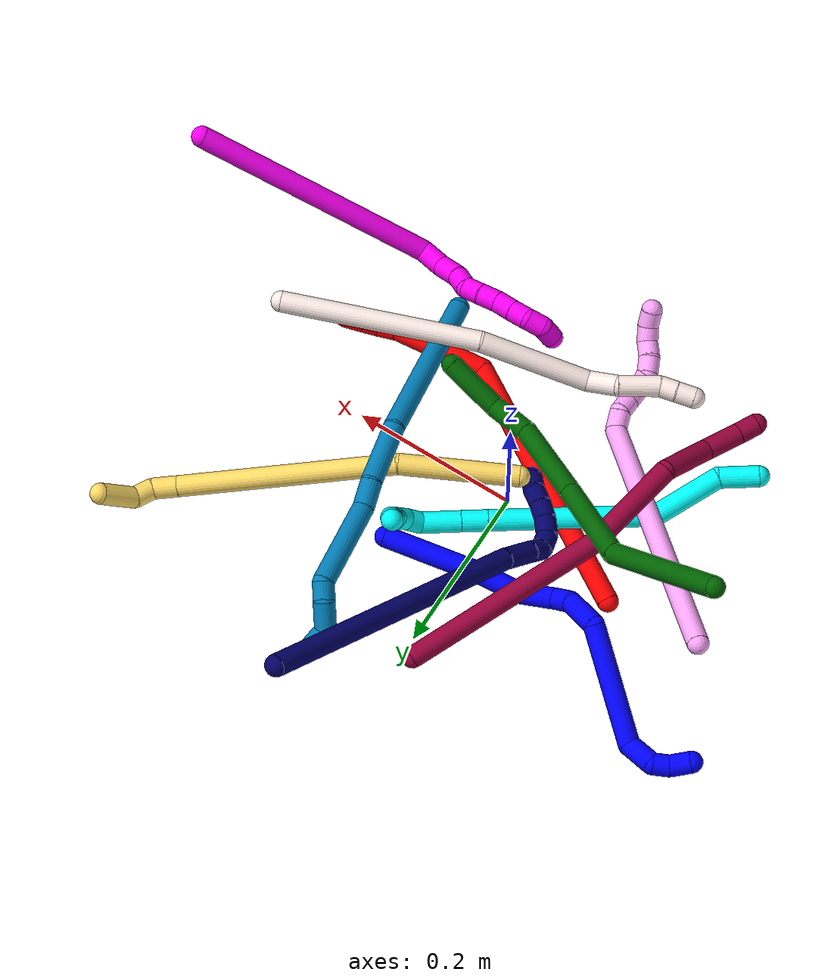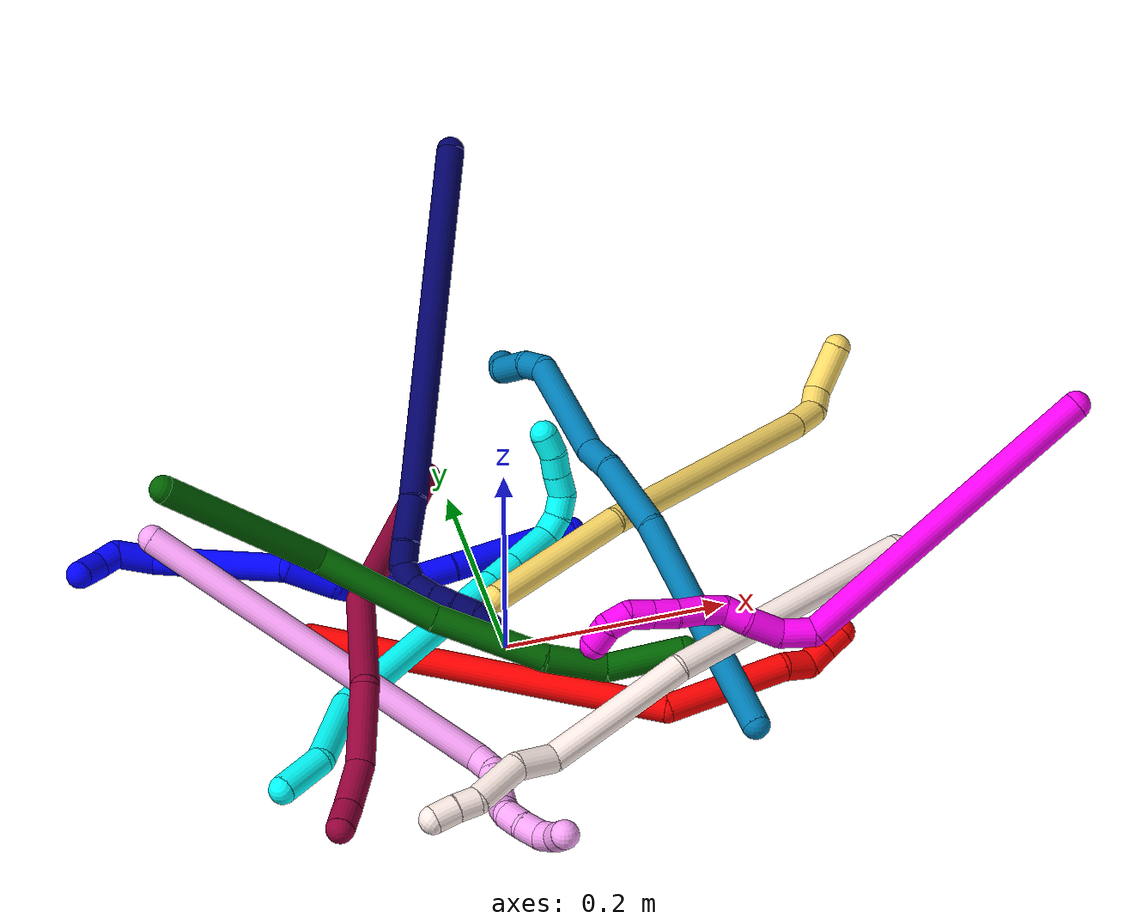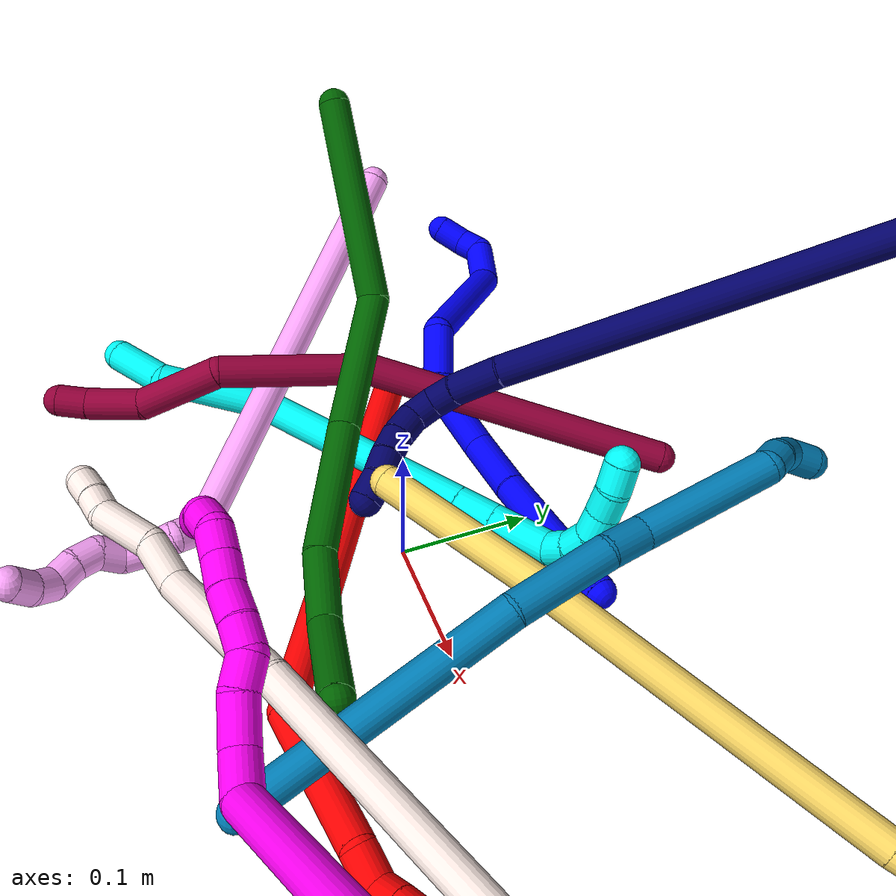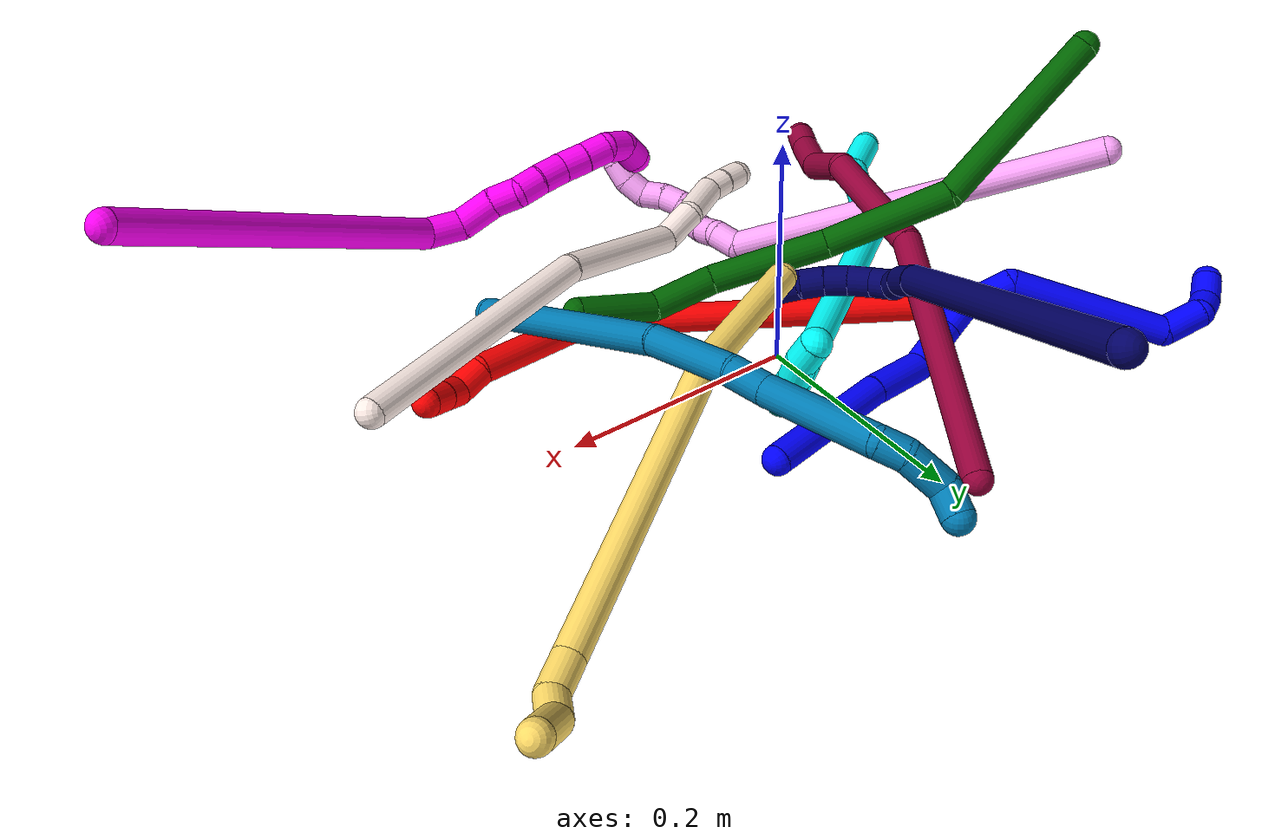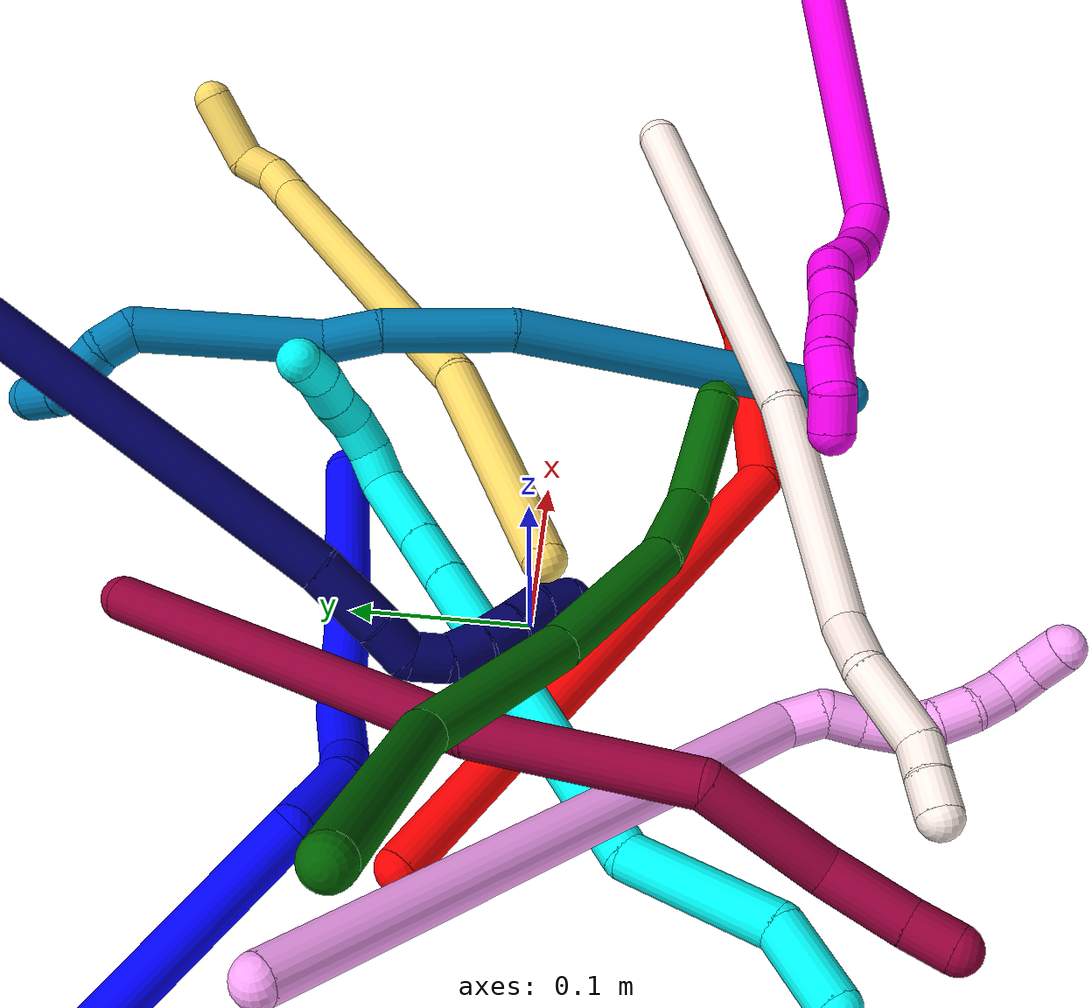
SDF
<sdf version="1.7">
 <world name="default">
  <plugin name="TubeGeneratorPlugin" filename="libtube_generator_plugin.so"/>
  <model name="photoneo_s_sensor">
   <static>1</static>
   <pose>0 0 2 1.57079 1.57079 3.14159</pose>
   <link name="link">
    <inertial><mass>0.1</mass></inertial>
    <sensor name="sensor" type="depth">
     <update_rate>30</update_rate>
     <camera>
      <horizontal_fov>1.22</horizontal_fov>
      <image><width>1920</width><height>1200</height><format>B8G8R8</format></image>
      <clip><near>0.1</near><far>4</far></clip>
      <depth_camera><output>points</output></depth_camera>
     </camera>
     <plugin name="camera_plugin" filename="libgazebo_ros_depth_camera.so">
      <baseline>0.2</baseline>
      <alwaysOn>1</alwaysOn>
      <updateRate>0.0</updateRate>
      <cameraName>camera_ir</cameraName>
      <imageTopicName>/camera/color/image_raw</imageTopicName>
      <cameraInfoTopicName>/camera/color/camera_info</cameraInfoTopicName>
      <depthImageTopicName>/camera/depth/image_raw</depthImageTopicName>
      <depthImageCameraInfoTopicName>/camera/depth/camera_info</depthImageCameraInfoTopicName>
      <pointCloudTopicName>/camera/depth/points</pointCloudTopicName>
      <frameName>fr_optical</frameName>
      <pointCloudCutoff>0.1</pointCloudCutoff>
      <pointCloudCutoffMax>2.0</pointCloudCutoffMax>
      <distortionK1>0</distortionK1>
      <distortionK2>0</distortionK2>
      <distortionK3>0</distortionK3>
      <distortionT1>0</distortionT1>
      <distortionT2>0</distortionT2>
      <CxPrime>0</CxPrime>
      <Cx>0</Cx>
      <Cy>0</Cy>
      <focalLength>0</focalLength>
      <hackBaseline>0</hackBaseline>
     </plugin>
    </sensor>
   </link>
  </model>
  <gravity>0 0 -9.8</gravity>
  <magnetic_field>6e-06 2.3e-05 -4.2e-05</magnetic_field>
  <atmosphere type="adiabatic"/>
  <physics name="default_physics" default="0" type="ode">
   <max_step_size>0.003</max_step_size>
   <real_time_factor>1</real_time_factor>
   <real_time_update_rate>1000</real_time_update_rate>
   <max_contacts>10000</max_contacts>
   <ode>
    <solver>
     <type>quick</type>
     <iters>100</iters>
     <sor>1.3</sor>
     <use_dynamic_moi_rescaling>0</use_dynamic_moi_rescaling>
    </solver>
    <constraints>
     <contact_max_correcting_vel>0</contact_max_correcting_vel>
     <contact_surface_layer>0.001</contact_surface_layer>
     <cfm>0</cfm>
     <erp>0.2</erp>
    </constraints>
   </ode>
  </physics>
  <scene><ambient>0.4 0.4 0.4 1</ambient><background>0.7 0.7 0.7 1</background><shadows>0</shadows></scene>
  <audio><device>default</device></audio>
  <spherical_coordinates>
   <surface_model>EARTH_WGS84</surface_model>
   <latitude_deg>0</latitude_deg>
   <longitude_deg>0</longitude_deg>
   <elevation>0</elevation>
   <heading_deg>0</heading_deg>
  </spherical_coordinates>
  <model name="bin">
   <static>1</static>
   <link name="bottom">
    <collision name="collision-bottom">
     <pose>0 0 -0.01 0 -0 0</pose>
     <geometry><box><size>0.8 0.6 0.02</size></box></geometry>
     <surface>
      <friction><ode><mu>100</mu><mu2>100</mu2></ode></friction>
      <contact><collide_bitmask>65535</collide_bitmask></contact>
     </surface>
    </collision>
   </link>
   <link name="west_wall">
    <collision name="collision-west_wall">
     <pose>-0.41 0 0.1 0 -0 0</pose>
     <geometry><box><size>0.02 0.6 0.2</size></box></geometry>
     <surface>
      <friction><ode><mu>100</mu><mu2>100</mu2></ode></friction>
      <contact><collide_bitmask>65535</collide_bitmask></contact>
     </surface>
    </collision>
   </link>
   <link name="east_wall">
    <collision name="collision-east_wall">
     <pose>0.41 0 0.1 0 -0 0</pose>
     <geometry><box><size>0.02 0.6 0.2</size></box></geometry>
     <surface>
      <friction><ode><mu>100</mu><mu2>100</mu2></ode></friction>
      <contact><collide_bitmask>65535</collide_bitmask></contact>
     </surface>
    </collision>
   </link>
   <link name="south_wall">
    <collision name="collision-south_wall">
     <pose>0 -0.31 0.1 0 -0 0</pose>
     <geometry><box><size>0.8 0.02 0.2</size></box></geometry>
     <surface>
      <friction><ode><mu>100</mu><mu2>100</mu2></ode></friction>
      <contact><collide_bitmask>65535</collide_bitmask></contact>
     </surface>
    </collision>
   </link>
   <link name="north_wall">
    <collision name="collision-north_wall">
     <pose>0 0.31 0.1 0 -0 0</pose>
     <geometry><box><size>0.8 0.02 0.2</size></box></geometry>
     <surface>
      <friction><ode><mu>100</mu><mu2>100</mu2></ode></friction>
      <contact><collide_bitmask>65535</collide_bitmask></contact>
     </surface>
    </collision>
   </link>
  </model>
  <model name="1">
   <static>0</static>
   <link name="1">
    <collision name="collision-cylinder-e_1_1_4">
     <pose>0.001101 0.006374 0.057311 -0.110755 0.01909 -0.001058</pose>
     <geometry><cylinder><radius>0.0125</radius><length>0.115349</length></cylinder></geometry>
     <surface>
      <friction><ode><mu>1.16</mu><mu2>1.16</mu2><slip1>0</slip1><slip2>0</slip2></ode></friction>
      <contact><ode><kp>1e+06</kp><kd>1</kd><max_vel>0</max_vel><min_depth>0.001</min_depth></ode></contact>
     </surface>
    </collision>
    <visual name="visual-cylinder-e_1_1_4">
     <pose>0.001101 0.006374 0.057311 -0.110755 0.01909 -0.001058</pose>
     <geometry><cylinder><radius>0.0125</radius><length>0.115349</length></cylinder></geometry>
     <material><ambient>0 0 1 1</ambient></material>
    </visual>
    <collision name="collision-cylinder-e_2_4_5">
     <pose>0.00024 0.014702 0.141116 -0.073665 -0.073704 0.002717</pose>
     <geometry><cylinder><radius>0.0125</radius><length>0.053278</length></cylinder></geometry>
     <surface>
      <friction><ode><mu>1.16</mu><mu2>1.16</mu2><slip1>0</slip1><slip2>0</slip2></ode></friction>
      <contact><ode><kp>1e+06</kp><kd>1</kd><max_vel>0</max_vel><min_depth>0.001</min_depth></ode></contact>
     </surface>
    </collision>
    <visual name="visual-cylinder-e_2_4_5">
     <pose>0.00024 0.014702 0.141116 -0.073665 -0.073704 0.002717</pose>
     <geometry><cylinder><radius>0.0125</radius><length>0.053278</length></cylinder></geometry>
     <material><ambient>0 0 1 1</ambient></material>
    </visual>
    <collision name="collision-cylinder-e_3_5_6">
     <pose>0.002328 0.025517 0.18754 -0.418316 0.183559 -0.039068</pose>
     <geometry><cylinder><radius>0.0125</radius><length>0.044364</length></cylinder></geometry>
     <surface>
      <friction><ode><mu>1.16</mu><mu2>1.16</mu2><slip1>0</slip1><slip2>0</slip2></ode></friction>
      <contact><ode><kp>1e+06</kp><kd>1</kd><max_vel>0</max_vel><min_depth>0.001</min_depth></ode></contact>
     </surface>
    </collision>
    <visual name="visual-cylinder-e_3_5_6">
     <pose>0.002328 0.025517 0.18754 -0.418316 0.183559 -0.039068</pose>
     <geometry><cylinder><radius>0.0125</radius><length>0.044364</length></cylinder></geometry>
     <material><ambient>0 0 1 1</ambient></material>
    </visual>
    <collision name="collision-cylinder-e_4_6_7">
     <pose>0.007393 0.040935 0.216018 -0.654398 0.094072 -0.031949</pose>
     <geometry><cylinder><radius>0.0125</radius><length>0.021646</length></cylinder></geometry>
     <surface>
      <friction><ode><mu>1.16</mu><mu2>1.16</mu2><slip1>0</slip1><slip2>0</slip2></ode></friction>
      <contact><ode><kp>1e+06</kp><kd>1</kd><max_vel>0</max_vel><min_depth>0.001</min_depth></ode></contact>
     </surface>
    </collision>
    <visual name="visual-cylinder-e_4_6_7">
     <pose>0.007393 0.040935 0.216018 -0.654398 0.094072 -0.031949</pose>
     <geometry><cylinder><radius>0.0125</radius><length>0.021646</length></cylinder></geometry>
     <material><ambient>0 0 1 1</ambient></material>
    </visual>
    <collision name="collision-cylinder-e_5_7_8">
     <pose>0.000298 0.059845 0.241594 -0.627565 -0.368036 0.120649</pose>
     <geometry><cylinder><radius>0.0125</radius><length>0.04509</length></cylinder></geometry>
     <surface>
      <friction><ode><mu>1.16</mu><mu2>1.16</mu2><slip1>0</slip1><slip2>0</slip2></ode></friction>
      <contact><ode><kp>1e+06</kp><kd>1</kd><max_vel>0</max_vel><min_depth>0.001</min_depth></ode></contact>
     </surface>
    </collision>
    <visual name="visual-cylinder-e_5_7_8">
     <pose>0.000298 0.059845 0.241594 -0.627565 -0.368036 0.120649</pose>
     <geometry><cylinder><radius>0.0125</radius><length>0.04509</length></cylinder></geometry>
     <material><ambient>0 0 1 1</ambient></material>
    </visual>
    <collision name="collision-cylinder-e_6_8_9">
     <pose>-0.061765 0.068224 0.302342 0.090633 -0.887763 -0.043122</pose>
     <geometry><cylinder><radius>0.0125</radius><length>0.139113</length></cylinder></geometry>
     <surface>
      <friction><ode><mu>1.16</mu><mu2>1.16</mu2><slip1>0</slip1><slip2>0</slip2></ode></friction>
      <contact><ode><kp>1e+06</kp><kd>1</kd><max_vel>0</max_vel><min_depth>0.001</min_depth></ode></contact>
     </surface>
    </collision>
    <visual name="visual-cylinder-e_6_8_9">
     <pose>-0.061765 0.068224 0.302342 0.090633 -0.887763 -0.043122</pose>
     <geometry><cylinder><radius>0.0125</radius><length>0.139113</length></cylinder></geometry>
     <material><ambient>0 0 1 1</ambient></material>
    </visual>
    <collision name="collision-cylinder-e_7_9_10">
     <pose>-0.121027 0.072101 0.36146 -0.471505 -0.298071 0.072106</pose>
     <geometry><cylinder><radius>0.0125</radius><length>0.036162</length></cylinder></geometry>
     <surface>
      <friction><ode><mu>1.16</mu><mu2>1.16</mu2><slip1>0</slip1><slip2>0</slip2></ode></friction>
      <contact><ode><kp>1e+06</kp><kd>1</kd><max_vel>0</max_vel><min_depth>0.001</min_depth></ode></contact>
     </surface>
    </collision>
    <visual name="visual-cylinder-e_7_9_10">
     <pose>-0.121027 0.072101 0.36146 -0.471505 -0.298071 0.072106</pose>
     <geometry><cylinder><radius>0.0125</radius><length>0.036162</length></cylinder></geometry>
     <material><ambient>0 0 1 1</ambient></material>
    </visual>
    <collision name="collision-cylinder-e_8_10_11">
     <pose>-0.123597 0.079716 0.386501 0.02448 0.276822 0.00341</pose>
     <geometry><cylinder><radius>0.0125</radius><length>0.020055</length></cylinder></geometry>
     <surface>
      <friction><ode><mu>1.16</mu><mu2>1.16</mu2><slip1>0</slip1><slip2>0</slip2></ode></friction>
      <contact><ode><kp>1e+06</kp><kd>1</kd><max_vel>0</max_vel><min_depth>0.001</min_depth></ode></contact>
     </surface>
    </collision>
    <visual name="visual-cylinder-e_8_10_11">
     <pose>-0.123597 0.079716 0.386501 0.02448 0.276822 0.00341</pose>
     <geometry><cylinder><radius>0.0125</radius><length>0.020055</length></cylinder></geometry>
     <material><ambient>0 0 1 1</ambient></material>
    </visual>
    <collision name="collision-cylinder-e_9_11_2">
     <pose>-0.11435 0.082339 0.406391 -0.272153 0.548881 -0.077061</pose>
     <geometry><cylinder><radius>0.0125</radius><length>0.024942</length></cylinder></geometry>
     <surface>
      <friction><ode><mu>1.16</mu><mu2>1.16</mu2><slip1>0</slip1><slip2>0</slip2></ode></friction>
      <contact><ode><kp>1e+06</kp><kd>1</kd><max_vel>0</max_vel><min_depth>0.001</min_depth></ode></contact>
     </surface>
    </collision>
    <visual name="visual-cylinder-e_9_11_2">
     <pose>-0.11435 0.082339 0.406391 -0.272153 0.548881 -0.077061</pose>
     <geometry><cylinder><radius>0.0125</radius><length>0.024942</length></cylinder></geometry>
     <material><ambient>0 0 1 1</ambient></material>
    </visual>
    <collision name="collision-sphere-2">
     <pose>-0.107843 0.085199 0.416639 0 -0 0</pose>
     <geometry><sphere><radius>0.0125</radius></sphere></geometry>
     <surface>
      <friction><ode><mu>1.16</mu><mu2>1.16</mu2><slip1>0</slip1><slip2>0</slip2></ode></friction>
      <contact><ode><kp>1e+06</kp><kd>1</kd><max_vel>0</max_vel><min_depth>0.001</min_depth></ode></contact>
     </surface>
    </collision>
    <visual name="visual-sphere-2">
     <pose>-0.107843 0.085199 0.416639 0 -0 0</pose>
     <geometry><sphere><radius>0.0125</radius></sphere></geometry>
     <material><ambient>0 0 1 1</ambient></material>
    </visual>
    <collision name="collision-sphere-11">
     <pose>-0.120856 0.079479 0.396143 0 -0 0</pose>
     <geometry><sphere><radius>0.0125</radius></sphere></geometry>
     <surface>
      <friction><ode><mu>1.16</mu><mu2>1.16</mu2><slip1>0</slip1><slip2>0</slip2></ode></friction>
      <contact><ode><kp>1e+06</kp><kd>1</kd><max_vel>0</max_vel><min_depth>0.001</min_depth></ode></contact>
     </surface>
    </collision>
    <visual name="visual-sphere-11">
     <pose>-0.120856 0.079479 0.396143 0 -0 0</pose>
     <geometry><sphere><radius>0.0125</radius></sphere></geometry>
     <material><ambient>0 0 1 1</ambient></material>
    </visual>
    <collision name="collision-sphere-10">
     <pose>-0.126337 0.079952 0.376858 0 -0 0</pose>
     <geometry><sphere><radius>0.0125</radius></sphere></geometry>
     <surface>
      <friction><ode><mu>1.16</mu><mu2>1.16</mu2><slip1>0</slip1><slip2>0</slip2></ode></friction>
      <contact><ode><kp>1e+06</kp><kd>1</kd><max_vel>0</max_vel><min_depth>0.001</min_depth></ode></contact>
     </surface>
    </collision>
    <visual name="visual-sphere-10">
     <pose>-0.126337 0.079952 0.376858 0 -0 0</pose>
     <geometry><sphere><radius>0.0125</radius></sphere></geometry>
     <material><ambient>0 0 1 1</ambient></material>
    </visual>
    <collision name="collision-sphere-9">
     <pose>-0.115717 0.06425 0.346062 0 -0 0</pose>
     <geometry><sphere><radius>0.0125</radius></sphere></geometry>
     <surface>
      <friction><ode><mu>1.16</mu><mu2>1.16</mu2><slip1>0</slip1><slip2>0</slip2></ode></friction>
      <contact><ode><kp>1e+06</kp><kd>1</kd><max_vel>0</max_vel><min_depth>0.001</min_depth></ode></contact>
     </surface>
    </collision>
    <visual name="visual-sphere-9">
     <pose>-0.115717 0.06425 0.346062 0 -0 0</pose>
     <geometry><sphere><radius>0.0125</radius></sphere></geometry>
     <material><ambient>0 0 1 1</ambient></material>
    </visual>
    <collision name="collision-sphere-4">
     <pose>0.002202 0.012747 0.114621 0 -0 0</pose>
     <geometry><sphere><radius>0.0125</radius></sphere></geometry>
     <surface>
      <friction><ode><mu>1.16</mu><mu2>1.16</mu2><slip1>0</slip1><slip2>0</slip2></ode></friction>
      <contact><ode><kp>1e+06</kp><kd>1</kd><max_vel>0</max_vel><min_depth>0.001</min_depth></ode></contact>
     </surface>
    </collision>
    <visual name="visual-sphere-4">
     <pose>0.002202 0.012747 0.114621 0 -0 0</pose>
     <geometry><sphere><radius>0.0125</radius></sphere></geometry>
     <material><ambient>0 0 1 1</ambient></material>
    </visual>
    <collision name="collision-sphere-1">
     <geometry><sphere><radius>0.0125</radius></sphere></geometry>
     <surface>
      <friction><ode><mu>1.16</mu><mu2>1.16</mu2><slip1>0</slip1><slip2>0</slip2></ode></friction>
      <contact><ode><kp>1e+06</kp><kd>1</kd><max_vel>0</max_vel><min_depth>0.001</min_depth></ode></contact>
     </surface>
    </collision>
    <visual name="visual-sphere-1">
     <geometry><sphere><radius>0.0125</radius></sphere></geometry>
     <material><ambient>0 0 1 1</ambient></material>
    </visual>
    <collision name="collision-sphere-8">
     <pose>-0.007813 0.072197 0.258622 0 -0 0</pose>
     <geometry><sphere><radius>0.0125</radius></sphere></geometry>
     <surface>
      <friction><ode><mu>1.16</mu><mu2>1.16</mu2><slip1>0</slip1><slip2>0</slip2></ode></friction>
      <contact><ode><kp>1e+06</kp><kd>1</kd><max_vel>0</max_vel><min_depth>0.001</min_depth></ode></contact>
     </surface>
    </collision>
    <visual name="visual-sphere-8">
     <pose>-0.007813 0.072197 0.258622 0 -0 0</pose>
     <geometry><sphere><radius>0.0125</radius></sphere></geometry>
     <material><ambient>0 0 1 1</ambient></material>
    </visual>
    <collision name="collision-sphere-5">
     <pose>-0.001721 0.016658 0.167611 0 -0 0</pose>
     <geometry><sphere><radius>0.0125</radius></sphere></geometry>
     <surface>
      <friction><ode><mu>1.16</mu><mu2>1.16</mu2><slip1>0</slip1><slip2>0</slip2></ode></friction>
      <contact><ode><kp>1e+06</kp><kd>1</kd><max_vel>0</max_vel><min_depth>0.001</min_depth></ode></contact>
     </surface>
    </collision>
    <visual name="visual-sphere-5">
     <pose>-0.001721 0.016658 0.167611 0 -0 0</pose>
     <geometry><sphere><radius>0.0125</radius></sphere></geometry>
     <material><ambient>0 0 1 1</ambient></material>
    </visual>
    <collision name="collision-sphere-6">
     <pose>0.006376 0.034377 0.207469 0 -0 0</pose>
     <geometry><sphere><radius>0.0125</radius></sphere></geometry>
     <surface>
      <friction><ode><mu>1.16</mu><mu2>1.16</mu2><slip1>0</slip1><slip2>0</slip2></ode></friction>
      <contact><ode><kp>1e+06</kp><kd>1</kd><max_vel>0</max_vel><min_depth>0.001</min_depth></ode></contact>
     </surface>
    </collision>
    <visual name="visual-sphere-6">
     <pose>0.006376 0.034377 0.207469 0 -0 0</pose>
     <geometry><sphere><radius>0.0125</radius></sphere></geometry>
     <material><ambient>0 0 1 1</ambient></material>
    </visual>
    <collision name="collision-sphere-7">
     <pose>0.00841 0.047494 0.224567 0 -0 0</pose>
     <geometry><sphere><radius>0.0125</radius></sphere></geometry>
     <surface>
      <friction><ode><mu>1.16</mu><mu2>1.16</mu2><slip1>0</slip1><slip2>0</slip2></ode></friction>
      <contact><ode><kp>1e+06</kp><kd>1</kd><max_vel>0</max_vel><min_depth>0.001</min_depth></ode></contact>
     </surface>
    </collision>
    <visual name="visual-sphere-7">
     <pose>0.00841 0.047494 0.224567 0 -0 0</pose>
     <geometry><sphere><radius>0.0125</radius></sphere></geometry>
     <material><ambient>0 0 1 1</ambient></material>
    </visual>
    <inertial>
     <pose>-0.035767 0.043971 0.222074 0 -0 0</pose>
     <mass>0.5</mass>
     <inertia>
      <ixx>0.000306</ixx>
      <ixy>0</ixy>
      <ixz>0</ixz>
      <iyy>0.000403</iyy>
      <iyz>0</iyz>
      <izz>0.000196</izz>
     </inertia>
    </inertial>
   </link>
   <pose>0.092059 0.116845 0.012498 1.67343 -0.244819 -1.41464</pose>
  </model>
  <model name="2">
   <static>0</static>
   <link name="2">
    <collision name="collision-cylinder-e_1_1_4">
     <pose>0.128787 -0.078785 0.057385 0.941279 0.922944 0.495607</pose>
     <geometry><cylinder><radius>0.0125</radius><length>0.323025</length></cylinder></geometry>
     <surface>
      <friction><ode><mu>1.16</mu><mu2>1.16</mu2><slip1>0</slip1><slip2>0</slip2></ode></friction>
      <contact><ode><kp>1e+06</kp><kd>1</kd><max_vel>0</max_vel><min_depth>0.001</min_depth></ode></contact>
     </surface>
    </collision>
    <visual name="visual-cylinder-e_1_1_4">
     <pose>0.128787 -0.078785 0.057385 0.941279 0.922944 0.495607</pose>
     <geometry><cylinder><radius>0.0125</radius><length>0.323025</length></cylinder></geometry>
     <material><ambient>1 0 0 1</ambient></material>
    </visual>
    <collision name="collision-cylinder-e_2_4_5">
     <pose>0.283315 -0.168411 0.162152 0.224916 0.48704 0.056102</pose>
     <geometry><cylinder><radius>0.0125</radius><length>0.110002</length></cylinder></geometry>
     <surface>
      <friction><ode><mu>1.16</mu><mu2>1.16</mu2><slip1>0</slip1><slip2>0</slip2></ode></friction>
      <contact><ode><kp>1e+06</kp><kd>1</kd><max_vel>0</max_vel><min_depth>0.001</min_depth></ode></contact>
     </surface>
    </collision>
    <visual name="visual-cylinder-e_2_4_5">
     <pose>0.283315 -0.168411 0.162152 0.224916 0.48704 0.056102</pose>
     <geometry><cylinder><radius>0.0125</radius><length>0.110002</length></cylinder></geometry>
     <material><ambient>1 0 0 1</ambient></material>
    </visual>
    <collision name="collision-cylinder-e_3_5_6">
     <pose>0.317211 -0.1776 0.219668 -0.161452 0.671165 -0.056418</pose>
     <geometry><cylinder><radius>0.0125</radius><length>0.026225</length></cylinder></geometry>
     <surface>
      <friction><ode><mu>1.16</mu><mu2>1.16</mu2><slip1>0</slip1><slip2>0</slip2></ode></friction>
      <contact><ode><kp>1e+06</kp><kd>1</kd><max_vel>0</max_vel><min_depth>0.001</min_depth></ode></contact>
     </surface>
    </collision>
    <visual name="visual-cylinder-e_3_5_6">
     <pose>0.317211 -0.1776 0.219668 -0.161452 0.671165 -0.056418</pose>
     <geometry><cylinder><radius>0.0125</radius><length>0.026225</length></cylinder></geometry>
     <material><ambient>1 0 0 1</ambient></material>
    </visual>
    <collision name="collision-cylinder-e_4_6_7">
     <pose>0.325793 -0.178284 0.23966 0.232557 0.042102 0.004919</pose>
     <geometry><cylinder><radius>0.0125</radius><length>0.020278</length></cylinder></geometry>
     <surface>
      <friction><ode><mu>1.16</mu><mu2>1.16</mu2><slip1>0</slip1><slip2>0</slip2></ode></friction>
      <contact><ode><kp>1e+06</kp><kd>1</kd><max_vel>0</max_vel><min_depth>0.001</min_depth></ode></contact>
     </surface>
    </collision>
    <visual name="visual-cylinder-e_4_6_7">
     <pose>0.325793 -0.178284 0.23966 0.232557 0.042102 0.004919</pose>
     <geometry><cylinder><radius>0.0125</radius><length>0.020278</length></cylinder></geometry>
     <material><ambient>1 0 0 1</ambient></material>
    </visual>
    <collision name="collision-cylinder-e_5_7_2">
     <pose>0.327087 -0.183003 0.259433 0.235951 0.084861 0.010064</pose>
     <geometry><cylinder><radius>0.0125</radius><length>0.02047</length></cylinder></geometry>
     <surface>
      <friction><ode><mu>1.16</mu><mu2>1.16</mu2><slip1>0</slip1><slip2>0</slip2></ode></friction>
      <contact><ode><kp>1e+06</kp><kd>1</kd><max_vel>0</max_vel><min_depth>0.001</min_depth></ode></contact>
     </surface>
    </collision>
    <visual name="visual-cylinder-e_5_7_2">
     <pose>0.327087 -0.183003 0.259433 0.235951 0.084861 0.010064</pose>
     <geometry><cylinder><radius>0.0125</radius><length>0.02047</length></cylinder></geometry>
     <material><ambient>1 0 0 1</ambient></material>
    </visual>
    <collision name="collision-sphere-2">
     <pose>0.327954 -0.185387 0.269349 0 -0 0</pose>
     <geometry><sphere><radius>0.0125</radius></sphere></geometry>
     <surface>
      <friction><ode><mu>1.16</mu><mu2>1.16</mu2><slip1>0</slip1><slip2>0</slip2></ode></friction>
      <contact><ode><kp>1e+06</kp><kd>1</kd><max_vel>0</max_vel><min_depth>0.001</min_depth></ode></contact>
     </surface>
    </collision>
    <visual name="visual-sphere-2">
     <pose>0.327954 -0.185387 0.269349 0 -0 0</pose>
     <geometry><sphere><radius>0.0125</radius></sphere></geometry>
     <material><ambient>1 0 0 1</ambient></material>
    </visual>
    <collision name="collision-sphere-7">
     <pose>0.326219 -0.180619 0.249518 0 -0 0</pose>
     <geometry><sphere><radius>0.0125</radius></sphere></geometry>
     <surface>
      <friction><ode><mu>1.16</mu><mu2>1.16</mu2><slip1>0</slip1><slip2>0</slip2></ode></friction>
      <contact><ode><kp>1e+06</kp><kd>1</kd><max_vel>0</max_vel><min_depth>0.001</min_depth></ode></contact>
     </surface>
    </collision>
    <visual name="visual-sphere-7">
     <pose>0.326219 -0.180619 0.249518 0 -0 0</pose>
     <geometry><sphere><radius>0.0125</radius></sphere></geometry>
     <material><ambient>1 0 0 1</ambient></material>
    </visual>
    <collision name="collision-sphere-6">
     <pose>0.325366 -0.175949 0.229803 0 -0 0</pose>
     <geometry><sphere><radius>0.0125</radius></sphere></geometry>
     <surface>
      <friction><ode><mu>1.16</mu><mu2>1.16</mu2><slip1>0</slip1><slip2>0</slip2></ode></friction>
      <contact><ode><kp>1e+06</kp><kd>1</kd><max_vel>0</max_vel><min_depth>0.001</min_depth></ode></contact>
     </surface>
    </collision>
    <visual name="visual-sphere-6">
     <pose>0.325366 -0.175949 0.229803 0 -0 0</pose>
     <geometry><sphere><radius>0.0125</radius></sphere></geometry>
     <material><ambient>1 0 0 1</ambient></material>
    </visual>
    <collision name="collision-sphere-5">
     <pose>0.309056 -0.179251 0.209533 0 -0 0</pose>
     <geometry><sphere><radius>0.0125</radius></sphere></geometry>
     <surface>
      <friction><ode><mu>1.16</mu><mu2>1.16</mu2><slip1>0</slip1><slip2>0</slip2></ode></friction>
      <contact><ode><kp>1e+06</kp><kd>1</kd><max_vel>0</max_vel><min_depth>0.001</min_depth></ode></contact>
     </surface>
    </collision>
    <visual name="visual-sphere-5">
     <pose>0.309056 -0.179251 0.209533 0 -0 0</pose>
     <geometry><sphere><radius>0.0125</radius></sphere></geometry>
     <material><ambient>1 0 0 1</ambient></material>
    </visual>
    <collision name="collision-sphere-1">
     <geometry><sphere><radius>0.0125</radius></sphere></geometry>
     <surface>
      <friction><ode><mu>1.16</mu><mu2>1.16</mu2><slip1>0</slip1><slip2>0</slip2></ode></friction>
      <contact><ode><kp>1e+06</kp><kd>1</kd><max_vel>0</max_vel><min_depth>0.001</min_depth></ode></contact>
     </surface>
    </collision>
    <visual name="visual-sphere-1">
     <geometry><sphere><radius>0.0125</radius></sphere></geometry>
     <material><ambient>1 0 0 1</ambient></material>
    </visual>
    <collision name="collision-sphere-4">
     <pose>0.257574 -0.15757 0.11477 0 -0 0</pose>
     <geometry><sphere><radius>0.0125</radius></sphere></geometry>
     <surface>
      <friction><ode><mu>1.16</mu><mu2>1.16</mu2><slip1>0</slip1><slip2>0</slip2></ode></friction>
      <contact><ode><kp>1e+06</kp><kd>1</kd><max_vel>0</max_vel><min_depth>0.001</min_depth></ode></contact>
     </surface>
    </collision>
    <visual name="visual-sphere-4">
     <pose>0.257574 -0.15757 0.11477 0 -0 0</pose>
     <geometry><sphere><radius>0.0125</radius></sphere></geometry>
     <material><ambient>1 0 0 1</ambient></material>
    </visual>
    <inertial>
     <pose>0.188775 -0.111988 0.10461 0 -0 0</pose>
     <mass>0.5</mass>
     <inertia>
      <ixx>0.002445</ixx>
      <ixy>0</ixy>
      <ixz>0</ixz>
      <iyy>0.003245</iyy>
      <iyz>0</iyz>
      <izz>-0.000885</izz>
     </inertia>
    </inertial>
   </link>
   <pose>-0.164053 0.047022 0.011489 -1.30174 0.616195 -0.76606</pose>
  </model>
  <model name="3">
   <static>0</static>
   <link name="3">
    <collision name="collision-cylinder-e_1_1_4">
     <pose>0.019445 0.005965 -0.011153 -2.65043 0.994121 -2.276</pose>
     <geometry><cylinder><radius>0.0125</radius><length>0.046393</length></cylinder></geometry>
     <surface>
      <friction><ode><mu>1.16</mu><mu2>1.16</mu2><slip1>0</slip1><slip2>0</slip2></ode></friction>
      <contact><ode><kp>1e+06</kp><kd>1</kd><max_vel>0</max_vel><min_depth>0.001</min_depth></ode></contact>
     </surface>
    </collision>
    <visual name="visual-cylinder-e_1_1_4">
     <pose>0.019445 0.005965 -0.011153 -2.65043 0.994121 -2.276</pose>
     <geometry><cylinder><radius>0.0125</radius><length>0.046393</length></cylinder></geometry>
     <material><ambient>0.003922 1 0.996078 1</ambient></material>
    </visual>
    <collision name="collision-cylinder-e_2_4_5">
     <pose>0.061232 0.039253 -0.045085 -2.26576 0.560793 -1.10281</pose>
     <geometry><cylinder><radius>0.0125</radius><length>0.084014</length></cylinder></geometry>
     <surface>
      <friction><ode><mu>1.16</mu><mu2>1.16</mu2><slip1>0</slip1><slip2>0</slip2></ode></friction>
      <contact><ode><kp>1e+06</kp><kd>1</kd><max_vel>0</max_vel><min_depth>0.001</min_depth></ode></contact>
     </surface>
    </collision>
    <visual name="visual-cylinder-e_2_4_5">
     <pose>0.061232 0.039253 -0.045085 -2.26576 0.560793 -1.10281</pose>
     <geometry><cylinder><radius>0.0125</radius><length>0.084014</length></cylinder></geometry>
     <material><ambient>0.003922 1 0.996078 1</ambient></material>
    </visual>
    <collision name="collision-cylinder-e_3_5_6">
     <pose>0.165472 0.092641 -0.1101 -2.58869 1.02597 -2.20841</pose>
     <geometry><cylinder><radius>0.0125</radius><length>0.191527</length></cylinder></geometry>
     <surface>
      <friction><ode><mu>1.16</mu><mu2>1.16</mu2><slip1>0</slip1><slip2>0</slip2></ode></friction>
      <contact><ode><kp>1e+06</kp><kd>1</kd><max_vel>0</max_vel><min_depth>0.001</min_depth></ode></contact>
     </surface>
    </collision>
    <visual name="visual-cylinder-e_3_5_6">
     <pose>0.165472 0.092641 -0.1101 -2.58869 1.02597 -2.20841</pose>
     <geometry><cylinder><radius>0.0125</radius><length>0.191527</length></cylinder></geometry>
     <material><ambient>0.003922 1 0.996078 1</ambient></material>
    </visual>
    <collision name="collision-cylinder-e_4_6_7">
     <pose>0.260386 0.122881 -0.159241 -2.59763 1.01582 -2.21262</pose>
     <geometry><cylinder><radius>0.0125</radius><length>0.030628</length></cylinder></geometry>
     <surface>
      <friction><ode><mu>1.16</mu><mu2>1.16</mu2><slip1>0</slip1><slip2>0</slip2></ode></friction>
      <contact><ode><kp>1e+06</kp><kd>1</kd><max_vel>0</max_vel><min_depth>0.001</min_depth></ode></contact>
     </surface>
    </collision>
    <visual name="visual-cylinder-e_4_6_7">
     <pose>0.260386 0.122881 -0.159241 -2.59763 1.01582 -2.21262</pose>
     <geometry><cylinder><radius>0.0125</radius><length>0.030628</length></cylinder></geometry>
     <material><ambient>0.003922 1 0.996078 1</ambient></material>
    </visual>
    <collision name="collision-cylinder-e_5_7_8">
     <pose>0.293364 0.133565 -0.176662 -2.58747 1.01617 -2.19727</pose>
     <geometry><cylinder><radius>0.0125</radius><length>0.046964</length></cylinder></geometry>
     <surface>
      <friction><ode><mu>1.16</mu><mu2>1.16</mu2><slip1>0</slip1><slip2>0</slip2></ode></friction>
      <contact><ode><kp>1e+06</kp><kd>1</kd><max_vel>0</max_vel><min_depth>0.001</min_depth></ode></contact>
     </surface>
    </collision>
    <visual name="visual-cylinder-e_5_7_8">
     <pose>0.293364 0.133565 -0.176662 -2.58747 1.01617 -2.19727</pose>
     <geometry><cylinder><radius>0.0125</radius><length>0.046964</length></cylinder></geometry>
     <material><ambient>0.003922 1 0.996078 1</ambient></material>
    </visual>
    <collision name="collision-cylinder-e_6_8_9">
     <pose>0.322975 0.142814 -0.185402 -0.996265 1.24429 -0.743788</pose>
     <geometry><cylinder><radius>0.0125</radius><length>0.020375</length></cylinder></geometry>
     <surface>
      <friction><ode><mu>1.16</mu><mu2>1.16</mu2><slip1>0</slip1><slip2>0</slip2></ode></friction>
      <contact><ode><kp>1e+06</kp><kd>1</kd><max_vel>0</max_vel><min_depth>0.001</min_depth></ode></contact>
     </surface>
    </collision>
    <visual name="visual-cylinder-e_6_8_9">
     <pose>0.322975 0.142814 -0.185402 -0.996265 1.24429 -0.743788</pose>
     <geometry><cylinder><radius>0.0125</radius><length>0.020375</length></cylinder></geometry>
     <material><ambient>0.003922 1 0.996078 1</ambient></material>
    </visual>
    <collision name="collision-cylinder-e_7_9_10">
     <pose>0.340376 0.150027 -0.179127 -0.782179 0.885112 -0.385948</pose>
     <geometry><cylinder><radius>0.0125</radius><length>0.020031</length></cylinder></geometry>
     <surface>
      <friction><ode><mu>1.16</mu><mu2>1.16</mu2><slip1>0</slip1><slip2>0</slip2></ode></friction>
      <contact><ode><kp>1e+06</kp><kd>1</kd><max_vel>0</max_vel><min_depth>0.001</min_depth></ode></contact>
     </surface>
    </collision>
    <visual name="visual-cylinder-e_7_9_10">
     <pose>0.340376 0.150027 -0.179127 -0.782179 0.885112 -0.385948</pose>
     <geometry><cylinder><radius>0.0125</radius><length>0.020031</length></cylinder></geometry>
     <material><ambient>0.003922 1 0.996078 1</ambient></material>
    </visual>
    <collision name="collision-cylinder-e_8_10_11">
     <pose>0.352018 0.159713 -0.167015 -0.600634 0.398899 -0.125034</pose>
     <geometry><cylinder><radius>0.0125</radius><length>0.020031</length></cylinder></geometry>
     <surface>
      <friction><ode><mu>1.16</mu><mu2>1.16</mu2><slip1>0</slip1><slip2>0</slip2></ode></friction>
      <contact><ode><kp>1e+06</kp><kd>1</kd><max_vel>0</max_vel><min_depth>0.001</min_depth></ode></contact>
     </surface>
    </collision>
    <visual name="visual-cylinder-e_8_10_11">
     <pose>0.352018 0.159713 -0.167015 -0.600634 0.398899 -0.125034</pose>
     <geometry><cylinder><radius>0.0125</radius><length>0.020031</length></cylinder></geometry>
     <material><ambient>0.003922 1 0.996078 1</ambient></material>
    </visual>
    <collision name="collision-cylinder-e_9_11_12">
     <pose>0.360357 0.168968 -0.15139 -0.466961 0.460374 -0.111345</pose>
     <geometry><cylinder><radius>0.0125</radius><length>0.020028</length></cylinder></geometry>
     <surface>
      <friction><ode><mu>1.16</mu><mu2>1.16</mu2><slip1>0</slip1><slip2>0</slip2></ode></friction>
      <contact><ode><kp>1e+06</kp><kd>1</kd><max_vel>0</max_vel><min_depth>0.001</min_depth></ode></contact>
     </surface>
    </collision>
    <visual name="visual-cylinder-e_9_11_12">
     <pose>0.360357 0.168968 -0.15139 -0.466961 0.460374 -0.111345</pose>
     <geometry><cylinder><radius>0.0125</radius><length>0.020028</length></cylinder></geometry>
     <material><ambient>0.003922 1 0.996078 1</ambient></material>
    </visual>
    <collision name="collision-cylinder-e_10_12_2">
     <pose>0.367048 0.178397 -0.135254 -0.585779 0.226034 -0.068428</pose>
     <geometry><cylinder><radius>0.0125</radius><length>0.020009</length></cylinder></geometry>
     <surface>
      <friction><ode><mu>1.16</mu><mu2>1.16</mu2><slip1>0</slip1><slip2>0</slip2></ode></friction>
      <contact><ode><kp>1e+06</kp><kd>1</kd><max_vel>0</max_vel><min_depth>0.001</min_depth></ode></contact>
     </surface>
    </collision>
    <visual name="visual-cylinder-e_10_12_2">
     <pose>0.367048 0.178397 -0.135254 -0.585779 0.226034 -0.068428</pose>
     <geometry><cylinder><radius>0.0125</radius><length>0.020009</length></cylinder></geometry>
     <material><ambient>0.003922 1 0.996078 1</ambient></material>
    </visual>
    <collision name="collision-sphere-2">
     <pose>0.36929 0.183787 -0.12713 0 -0 0</pose>
     <geometry><sphere><radius>0.0125</radius></sphere></geometry>
     <surface>
      <friction><ode><mu>1.16</mu><mu2>1.16</mu2><slip1>0</slip1><slip2>0</slip2></ode></friction>
      <contact><ode><kp>1e+06</kp><kd>1</kd><max_vel>0</max_vel><min_depth>0.001</min_depth></ode></contact>
     </surface>
    </collision>
    <visual name="visual-sphere-2">
     <pose>0.36929 0.183787 -0.12713 0 -0 0</pose>
     <geometry><sphere><radius>0.0125</radius></sphere></geometry>
     <material><ambient>0.003922 1 0.996078 1</ambient></material>
    </visual>
    <collision name="collision-sphere-12">
     <pose>0.364806 0.173007 -0.143379 0 -0 0</pose>
     <geometry><sphere><radius>0.0125</radius></sphere></geometry>
     <surface>
      <friction><ode><mu>1.16</mu><mu2>1.16</mu2><slip1>0</slip1><slip2>0</slip2></ode></friction>
      <contact><ode><kp>1e+06</kp><kd>1</kd><max_vel>0</max_vel><min_depth>0.001</min_depth></ode></contact>
     </surface>
    </collision>
    <visual name="visual-sphere-12">
     <pose>0.364806 0.173007 -0.143379 0 -0 0</pose>
     <geometry><sphere><radius>0.0125</radius></sphere></geometry>
     <material><ambient>0.003922 1 0.996078 1</ambient></material>
    </visual>
    <collision name="collision-sphere-11">
     <pose>0.355908 0.164929 -0.159401 0 -0 0</pose>
     <geometry><sphere><radius>0.0125</radius></sphere></geometry>
     <surface>
      <friction><ode><mu>1.16</mu><mu2>1.16</mu2><slip1>0</slip1><slip2>0</slip2></ode></friction>
      <contact><ode><kp>1e+06</kp><kd>1</kd><max_vel>0</max_vel><min_depth>0.001</min_depth></ode></contact>
     </surface>
    </collision>
    <visual name="visual-sphere-11">
     <pose>0.355908 0.164929 -0.159401 0 -0 0</pose>
     <geometry><sphere><radius>0.0125</radius></sphere></geometry>
     <material><ambient>0.003922 1 0.996078 1</ambient></material>
    </visual>
    <collision name="collision-sphere-10">
     <pose>0.348127 0.154497 -0.174629 0 -0 0</pose>
     <geometry><sphere><radius>0.0125</radius></sphere></geometry>
     <surface>
      <friction><ode><mu>1.16</mu><mu2>1.16</mu2><slip1>0</slip1><slip2>0</slip2></ode></friction>
      <contact><ode><kp>1e+06</kp><kd>1</kd><max_vel>0</max_vel><min_depth>0.001</min_depth></ode></contact>
     </surface>
    </collision>
    <visual name="visual-sphere-10">
     <pose>0.348127 0.154497 -0.174629 0 -0 0</pose>
     <geometry><sphere><radius>0.0125</radius></sphere></geometry>
     <material><ambient>0.003922 1 0.996078 1</ambient></material>
    </visual>
    <collision name="collision-sphere-9">
     <pose>0.332624 0.145557 -0.183626 0 -0 0</pose>
     <geometry><sphere><radius>0.0125</radius></sphere></geometry>
     <surface>
      <friction><ode><mu>1.16</mu><mu2>1.16</mu2><slip1>0</slip1><slip2>0</slip2></ode></friction>
      <contact><ode><kp>1e+06</kp><kd>1</kd><max_vel>0</max_vel><min_depth>0.001</min_depth></ode></contact>
     </surface>
    </collision>
    <visual name="visual-sphere-9">
     <pose>0.332624 0.145557 -0.183626 0 -0 0</pose>
     <geometry><sphere><radius>0.0125</radius></sphere></geometry>
     <material><ambient>0.003922 1 0.996078 1</ambient></material>
    </visual>
    <collision name="collision-sphere-4">
     <pose>0.03889 0.01193 -0.022305 0 -0 0</pose>
     <geometry><sphere><radius>0.0125</radius></sphere></geometry>
     <surface>
      <friction><ode><mu>1.16</mu><mu2>1.16</mu2><slip1>0</slip1><slip2>0</slip2></ode></friction>
      <contact><ode><kp>1e+06</kp><kd>1</kd><max_vel>0</max_vel><min_depth>0.001</min_depth></ode></contact>
     </surface>
    </collision>
    <visual name="visual-sphere-4">
     <pose>0.03889 0.01193 -0.022305 0 -0 0</pose>
     <geometry><sphere><radius>0.0125</radius></sphere></geometry>
     <material><ambient>0.003922 1 0.996078 1</ambient></material>
    </visual>
    <collision name="collision-sphere-1">
     <geometry><sphere><radius>0.0125</radius></sphere></geometry>
     <surface>
      <friction><ode><mu>1.16</mu><mu2>1.16</mu2><slip1>0</slip1><slip2>0</slip2></ode></friction>
      <contact><ode><kp>1e+06</kp><kd>1</kd><max_vel>0</max_vel><min_depth>0.001</min_depth></ode></contact>
     </surface>
    </collision>
    <visual name="visual-sphere-1">
     <geometry><sphere><radius>0.0125</radius></sphere></geometry>
     <material><ambient>0.003922 1 0.996078 1</ambient></material>
    </visual>
    <collision name="collision-sphere-8">
     <pose>0.313326 0.140072 -0.187178 0 -0 0</pose>
     <geometry><sphere><radius>0.0125</radius></sphere></geometry>
     <surface>
      <friction><ode><mu>1.16</mu><mu2>1.16</mu2><slip1>0</slip1><slip2>0</slip2></ode></friction>
      <contact><ode><kp>1e+06</kp><kd>1</kd><max_vel>0</max_vel><min_depth>0.001</min_depth></ode></contact>
     </surface>
    </collision>
    <visual name="visual-sphere-8">
     <pose>0.313326 0.140072 -0.187178 0 -0 0</pose>
     <geometry><sphere><radius>0.0125</radius></sphere></geometry>
     <material><ambient>0.003922 1 0.996078 1</ambient></material>
    </visual>
    <collision name="collision-sphere-5">
     <pose>0.083574 0.066576 -0.067864 0 -0 0</pose>
     <geometry><sphere><radius>0.0125</radius></sphere></geometry>
     <surface>
      <friction><ode><mu>1.16</mu><mu2>1.16</mu2><slip1>0</slip1><slip2>0</slip2></ode></friction>
      <contact><ode><kp>1e+06</kp><kd>1</kd><max_vel>0</max_vel><min_depth>0.001</min_depth></ode></contact>
     </surface>
    </collision>
    <visual name="visual-sphere-5">
     <pose>0.083574 0.066576 -0.067864 0 -0 0</pose>
     <geometry><sphere><radius>0.0125</radius></sphere></geometry>
     <material><ambient>0.003922 1 0.996078 1</ambient></material>
    </visual>
    <collision name="collision-sphere-6">
     <pose>0.247371 0.118705 -0.152337 0 -0 0</pose>
     <geometry><sphere><radius>0.0125</radius></sphere></geometry>
     <surface>
      <friction><ode><mu>1.16</mu><mu2>1.16</mu2><slip1>0</slip1><slip2>0</slip2></ode></friction>
      <contact><ode><kp>1e+06</kp><kd>1</kd><max_vel>0</max_vel><min_depth>0.001</min_depth></ode></contact>
     </surface>
    </collision>
    <visual name="visual-sphere-6">
     <pose>0.247371 0.118705 -0.152337 0 -0 0</pose>
     <geometry><sphere><radius>0.0125</radius></sphere></geometry>
     <material><ambient>0.003922 1 0.996078 1</ambient></material>
    </visual>
    <collision name="collision-sphere-7">
     <pose>0.273402 0.127057 -0.166146 0 -0 0</pose>
     <geometry><sphere><radius>0.0125</radius></sphere></geometry>
     <surface>
      <friction><ode><mu>1.16</mu><mu2>1.16</mu2><slip1>0</slip1><slip2>0</slip2></ode></friction>
      <contact><ode><kp>1e+06</kp><kd>1</kd><max_vel>0</max_vel><min_depth>0.001</min_depth></ode></contact>
     </surface>
    </collision>
    <visual name="visual-sphere-7">
     <pose>0.273402 0.127057 -0.166146 0 -0 0</pose>
     <geometry><sphere><radius>0.0125</radius></sphere></geometry>
     <material><ambient>0.003922 1 0.996078 1</ambient></material>
    </visual>
    <inertial>
     <pose>0.189006 0.094844 -0.110032 0 -0 0</pose>
     <mass>0.5</mass>
     <inertia>
      <ixx>-0.000435</ixx>
      <ixy>0</ixy>
      <ixz>0</ixz>
      <iyy>0.000262</iyy>
      <iyz>0</iyz>
      <izz>-0.000775</izz>
     </inertia>
    </inertial>
   </link>
   <pose>-0.236222 -0.163029 0.05016 0.105089 -0.465921 0.283203</pose>
  </model>
  <model name="4">
   <static>0</static>
   <link name="4">
    <collision name="collision-cylinder-e_1_1_4">
     <pose>0.117906 -0.100562 -0.064961 2.14434 0.777769 1.2902</pose>
     <geometry><cylinder><radius>0.0125</radius><length>0.336062</length></cylinder></geometry>
     <surface>
      <friction><ode><mu>1.16</mu><mu2>1.16</mu2><slip1>0</slip1><slip2>0</slip2></ode></friction>
      <contact><ode><kp>1e+06</kp><kd>1</kd><max_vel>0</max_vel><min_depth>0.001</min_depth></ode></contact>
     </surface>
    </collision>
    <visual name="visual-cylinder-e_1_1_4">
     <pose>0.117906 -0.100562 -0.064961 2.14434 0.777769 1.2902</pose>
     <geometry><cylinder><radius>0.0125</radius><length>0.336062</length></cylinder></geometry>
     <material><ambient>1 0.65098 0.996078 1</ambient></material>
    </visual>
    <collision name="collision-cylinder-e_2_4_5">
     <pose>0.239296 -0.211948 -0.128556 1.44534 0.309128 0.273071</pose>
     <geometry><cylinder><radius>0.0125</radius><length>0.022907</length></cylinder></geometry>
     <surface>
      <friction><ode><mu>1.16</mu><mu2>1.16</mu2><slip1>0</slip1><slip2>0</slip2></ode></friction>
      <contact><ode><kp>1e+06</kp><kd>1</kd><max_vel>0</max_vel><min_depth>0.001</min_depth></ode></contact>
     </surface>
    </collision>
    <visual name="visual-cylinder-e_2_4_5">
     <pose>0.239296 -0.211948 -0.128556 1.44534 0.309128 0.273071</pose>
     <geometry><cylinder><radius>0.0125</radius><length>0.022907</length></cylinder></geometry>
     <material><ambient>1 0.65098 0.996078 1</ambient></material>
    </visual>
    <collision name="collision-cylinder-e_3_5_6">
     <pose>0.243009 -0.232101 -0.131201 1.9768 0.022512 0.03418</pose>
     <geometry><cylinder><radius>0.0125</radius><length>0.02031</length></cylinder></geometry>
     <surface>
      <friction><ode><mu>1.16</mu><mu2>1.16</mu2><slip1>0</slip1><slip2>0</slip2></ode></friction>
      <contact><ode><kp>1e+06</kp><kd>1</kd><max_vel>0</max_vel><min_depth>0.001</min_depth></ode></contact>
     </surface>
    </collision>
    <visual name="visual-cylinder-e_3_5_6">
     <pose>0.243009 -0.232101 -0.131201 1.9768 0.022512 0.03418</pose>
     <geometry><cylinder><radius>0.0125</radius><length>0.02031</length></cylinder></geometry>
     <material><ambient>1 0.65098 0.996078 1</ambient></material>
    </visual>
    <collision name="collision-cylinder-e_4_6_7">
     <pose>0.242845 -0.251253 -0.137092 1.76008 -0.039253 -0.047484</pose>
     <geometry><cylinder><radius>0.0125</radius><length>0.020023</length></cylinder></geometry>
     <surface>
      <friction><ode><mu>1.16</mu><mu2>1.16</mu2><slip1>0</slip1><slip2>0</slip2></ode></friction>
      <contact><ode><kp>1e+06</kp><kd>1</kd><max_vel>0</max_vel><min_depth>0.001</min_depth></ode></contact>
     </surface>
    </collision>
    <visual name="visual-cylinder-e_4_6_7">
     <pose>0.242845 -0.251253 -0.137092 1.76008 -0.039253 -0.047484</pose>
     <geometry><cylinder><radius>0.0125</radius><length>0.020023</length></cylinder></geometry>
     <material><ambient>1 0.65098 0.996078 1</ambient></material>
    </visual>
    <collision name="collision-cylinder-e_5_7_8">
     <pose>0.24176 -0.270291 -0.134477 1.11671 -0.067423 -0.042126</pose>
     <geometry><cylinder><radius>0.0125</radius><length>0.020552</length></cylinder></geometry>
     <surface>
      <friction><ode><mu>1.16</mu><mu2>1.16</mu2><slip1>0</slip1><slip2>0</slip2></ode></friction>
      <contact><ode><kp>1e+06</kp><kd>1</kd><max_vel>0</max_vel><min_depth>0.001</min_depth></ode></contact>
     </surface>
    </collision>
    <visual name="visual-cylinder-e_5_7_8">
     <pose>0.24176 -0.270291 -0.134477 1.11671 -0.067423 -0.042126</pose>
     <geometry><cylinder><radius>0.0125</radius><length>0.020552</length></cylinder></geometry>
     <material><ambient>1 0.65098 0.996078 1</ambient></material>
    </visual>
    <collision name="collision-cylinder-e_6_8_9">
     <pose>0.245241 -0.288588 -0.129294 1.49542 0.429608 0.399242</pose>
     <geometry><cylinder><radius>0.0125</radius><length>0.020038</length></cylinder></geometry>
     <surface>
      <friction><ode><mu>1.16</mu><mu2>1.16</mu2><slip1>0</slip1><slip2>0</slip2></ode></friction>
      <contact><ode><kp>1e+06</kp><kd>1</kd><max_vel>0</max_vel><min_depth>0.001</min_depth></ode></contact>
     </surface>
    </collision>
    <visual name="visual-cylinder-e_6_8_9">
     <pose>0.245241 -0.288588 -0.129294 1.49542 0.429608 0.399242</pose>
     <geometry><cylinder><radius>0.0125</radius><length>0.020038</length></cylinder></geometry>
     <material><ambient>1 0.65098 0.996078 1</ambient></material>
    </visual>
    <collision name="collision-cylinder-e_7_9_10">
     <pose>0.255618 -0.305531 -0.129335 1.66299 0.666149 0.725288</pose>
     <geometry><cylinder><radius>0.0125</radius><length>0.020081</length></cylinder></geometry>
     <surface>
      <friction><ode><mu>1.16</mu><mu2>1.16</mu2><slip1>0</slip1><slip2>0</slip2></ode></friction>
      <contact><ode><kp>1e+06</kp><kd>1</kd><max_vel>0</max_vel><min_depth>0.001</min_depth></ode></contact>
     </surface>
    </collision>
    <visual name="visual-cylinder-e_7_9_10">
     <pose>0.255618 -0.305531 -0.129335 1.66299 0.666149 0.725288</pose>
     <geometry><cylinder><radius>0.0125</radius><length>0.020081</length></cylinder></geometry>
     <material><ambient>1 0.65098 0.996078 1</ambient></material>
    </visual>
    <collision name="collision-cylinder-e_8_10_11">
     <pose>0.265973 -0.321171 -0.12532 1.02337 0.427379 0.24253</pose>
     <geometry><cylinder><radius>0.0125</radius><length>0.020023</length></cylinder></geometry>
     <surface>
      <friction><ode><mu>1.16</mu><mu2>1.16</mu2><slip1>0</slip1><slip2>0</slip2></ode></friction>
      <contact><ode><kp>1e+06</kp><kd>1</kd><max_vel>0</max_vel><min_depth>0.001</min_depth></ode></contact>
     </surface>
    </collision>
    <visual name="visual-cylinder-e_8_10_11">
     <pose>0.265973 -0.321171 -0.12532 1.02337 0.427379 0.24253</pose>
     <geometry><cylinder><radius>0.0125</radius><length>0.020023</length></cylinder></geometry>
     <material><ambient>1 0.65098 0.996078 1</ambient></material>
    </visual>
    <collision name="collision-cylinder-e_9_11_2">
     <pose>0.271618 -0.336034 -0.113676 0.798485 0.150066 0.063411</pose>
     <geometry><cylinder><radius>0.0125</radius><length>0.020004</length></cylinder></geometry>
     <surface>
      <friction><ode><mu>1.16</mu><mu2>1.16</mu2><slip1>0</slip1><slip2>0</slip2></ode></friction>
      <contact><ode><kp>1e+06</kp><kd>1</kd><max_vel>0</max_vel><min_depth>0.001</min_depth></ode></contact>
     </surface>
    </collision>
    <visual name="visual-cylinder-e_9_11_2">
     <pose>0.271618 -0.336034 -0.113676 0.798485 0.150066 0.063411</pose>
     <geometry><cylinder><radius>0.0125</radius><length>0.020004</length></cylinder></geometry>
     <material><ambient>1 0.65098 0.996078 1</ambient></material>
    </visual>
    <collision name="collision-sphere-2">
     <pose>0.273113 -0.343118 -0.106776 0 -0 0</pose>
     <geometry><sphere><radius>0.0125</radius></sphere></geometry>
     <surface>
      <friction><ode><mu>1.16</mu><mu2>1.16</mu2><slip1>0</slip1><slip2>0</slip2></ode></friction>
      <contact><ode><kp>1e+06</kp><kd>1</kd><max_vel>0</max_vel><min_depth>0.001</min_depth></ode></contact>
     </surface>
    </collision>
    <visual name="visual-sphere-2">
     <pose>0.273113 -0.343118 -0.106776 0 -0 0</pose>
     <geometry><sphere><radius>0.0125</radius></sphere></geometry>
     <material><ambient>1 0.65098 0.996078 1</ambient></material>
    </visual>
    <collision name="collision-sphere-11">
     <pose>0.270122 -0.328951 -0.120577 0 -0 0</pose>
     <geometry><sphere><radius>0.0125</radius></sphere></geometry>
     <surface>
      <friction><ode><mu>1.16</mu><mu2>1.16</mu2><slip1>0</slip1><slip2>0</slip2></ode></friction>
      <contact><ode><kp>1e+06</kp><kd>1</kd><max_vel>0</max_vel><min_depth>0.001</min_depth></ode></contact>
     </surface>
    </collision>
    <visual name="visual-sphere-11">
     <pose>0.270122 -0.328951 -0.120577 0 -0 0</pose>
     <geometry><sphere><radius>0.0125</radius></sphere></geometry>
     <material><ambient>1 0.65098 0.996078 1</ambient></material>
    </visual>
    <collision name="collision-sphere-10">
     <pose>0.261823 -0.313391 -0.130062 0 -0 0</pose>
     <geometry><sphere><radius>0.0125</radius></sphere></geometry>
     <surface>
      <friction><ode><mu>1.16</mu><mu2>1.16</mu2><slip1>0</slip1><slip2>0</slip2></ode></friction>
      <contact><ode><kp>1e+06</kp><kd>1</kd><max_vel>0</max_vel><min_depth>0.001</min_depth></ode></contact>
     </surface>
    </collision>
    <visual name="visual-sphere-10">
     <pose>0.261823 -0.313391 -0.130062 0 -0 0</pose>
     <geometry><sphere><radius>0.0125</radius></sphere></geometry>
     <material><ambient>1 0.65098 0.996078 1</ambient></material>
    </visual>
    <collision name="collision-sphere-9">
     <pose>0.249414 -0.29767 -0.128608 0 -0 0</pose>
     <geometry><sphere><radius>0.0125</radius></sphere></geometry>
     <surface>
      <friction><ode><mu>1.16</mu><mu2>1.16</mu2><slip1>0</slip1><slip2>0</slip2></ode></friction>
      <contact><ode><kp>1e+06</kp><kd>1</kd><max_vel>0</max_vel><min_depth>0.001</min_depth></ode></contact>
     </surface>
    </collision>
    <visual name="visual-sphere-9">
     <pose>0.249414 -0.29767 -0.128608 0 -0 0</pose>
     <geometry><sphere><radius>0.0125</radius></sphere></geometry>
     <material><ambient>1 0.65098 0.996078 1</ambient></material>
    </visual>
    <collision name="collision-sphere-4">
     <pose>0.235812 -0.201123 -0.129922 0 -0 0</pose>
     <geometry><sphere><radius>0.0125</radius></sphere></geometry>
     <surface>
      <friction><ode><mu>1.16</mu><mu2>1.16</mu2><slip1>0</slip1><slip2>0</slip2></ode></friction>
      <contact><ode><kp>1e+06</kp><kd>1</kd><max_vel>0</max_vel><min_depth>0.001</min_depth></ode></contact>
     </surface>
    </collision>
    <visual name="visual-sphere-4">
     <pose>0.235812 -0.201123 -0.129922 0 -0 0</pose>
     <geometry><sphere><radius>0.0125</radius></sphere></geometry>
     <material><ambient>1 0.65098 0.996078 1</ambient></material>
    </visual>
    <collision name="collision-sphere-1">
     <geometry><sphere><radius>0.0125</radius></sphere></geometry>
     <surface>
      <friction><ode><mu>1.16</mu><mu2>1.16</mu2><slip1>0</slip1><slip2>0</slip2></ode></friction>
      <contact><ode><kp>1e+06</kp><kd>1</kd><max_vel>0</max_vel><min_depth>0.001</min_depth></ode></contact>
     </surface>
    </collision>
    <visual name="visual-sphere-1">
     <geometry><sphere><radius>0.0125</radius></sphere></geometry>
     <material><ambient>1 0.65098 0.996078 1</ambient></material>
    </visual>
    <collision name="collision-sphere-8">
     <pose>0.241068 -0.279505 -0.12998 0 -0 0</pose>
     <geometry><sphere><radius>0.0125</radius></sphere></geometry>
     <surface>
      <friction><ode><mu>1.16</mu><mu2>1.16</mu2><slip1>0</slip1><slip2>0</slip2></ode></friction>
      <contact><ode><kp>1e+06</kp><kd>1</kd><max_vel>0</max_vel><min_depth>0.001</min_depth></ode></contact>
     </surface>
    </collision>
    <visual name="visual-sphere-8">
     <pose>0.241068 -0.279505 -0.12998 0 -0 0</pose>
     <geometry><sphere><radius>0.0125</radius></sphere></geometry>
     <material><ambient>1 0.65098 0.996078 1</ambient></material>
    </visual>
    <collision name="collision-sphere-5">
     <pose>0.242781 -0.222774 -0.127191 0 -0 0</pose>
     <geometry><sphere><radius>0.0125</radius></sphere></geometry>
     <surface>
      <friction><ode><mu>1.16</mu><mu2>1.16</mu2><slip1>0</slip1><slip2>0</slip2></ode></friction>
      <contact><ode><kp>1e+06</kp><kd>1</kd><max_vel>0</max_vel><min_depth>0.001</min_depth></ode></contact>
     </surface>
    </collision>
    <visual name="visual-sphere-5">
     <pose>0.242781 -0.222774 -0.127191 0 -0 0</pose>
     <geometry><sphere><radius>0.0125</radius></sphere></geometry>
     <material><ambient>1 0.65098 0.996078 1</ambient></material>
    </visual>
    <collision name="collision-sphere-6">
     <pose>0.243238 -0.241428 -0.13521 0 -0 0</pose>
     <geometry><sphere><radius>0.0125</radius></sphere></geometry>
     <surface>
      <friction><ode><mu>1.16</mu><mu2>1.16</mu2><slip1>0</slip1><slip2>0</slip2></ode></friction>
      <contact><ode><kp>1e+06</kp><kd>1</kd><max_vel>0</max_vel><min_depth>0.001</min_depth></ode></contact>
     </surface>
    </collision>
    <visual name="visual-sphere-6">
     <pose>0.243238 -0.241428 -0.13521 0 -0 0</pose>
     <geometry><sphere><radius>0.0125</radius></sphere></geometry>
     <material><ambient>1 0.65098 0.996078 1</ambient></material>
    </visual>
    <collision name="collision-sphere-7">
     <pose>0.242452 -0.261078 -0.138975 0 -0 0</pose>
     <geometry><sphere><radius>0.0125</radius></sphere></geometry>
     <surface>
      <friction><ode><mu>1.16</mu><mu2>1.16</mu2><slip1>0</slip1><slip2>0</slip2></ode></friction>
      <contact><ode><kp>1e+06</kp><kd>1</kd><max_vel>0</max_vel><min_depth>0.001</min_depth></ode></contact>
     </surface>
    </collision>
    <visual name="visual-sphere-7">
     <pose>0.242452 -0.261078 -0.138975 0 -0 0</pose>
     <geometry><sphere><radius>0.0125</radius></sphere></geometry>
     <material><ambient>1 0.65098 0.996078 1</ambient></material>
    </visual>
    <inertial>
     <pose>0.161356 -0.158042 -0.085841 0 -0 0</pose>
     <mass>0.5</mass>
     <inertia>
      <ixx>0.002835</ixx>
      <ixy>0</ixy>
      <ixz>0</ixz>
      <iyy>0.003474</iyy>
      <iyz>0</iyz>
      <izz>-0.000328</izz>
     </inertia>
    </inertial>
   </link>
   <pose>-0.290811 0.077525 0.133566 -0.102317 0.04295 -0.010359</pose>
  </model>
  <model name="5">
   <static>0</static>
   <link name="5">
    <collision name="collision-cylinder-e_1_1_4">
     <pose>0.037156 0.019411 0.055386 -0.337096 0.564404 -0.098594</pose>
     <geometry><cylinder><radius>0.0125</radius><length>0.138924</length></cylinder></geometry>
     <surface>
      <friction><ode><mu>1.16</mu><mu2>1.16</mu2><slip1>0</slip1><slip2>0</slip2></ode></friction>
      <contact><ode><kp>1e+06</kp><kd>1</kd><max_vel>0</max_vel><min_depth>0.001</min_depth></ode></contact>
     </surface>
    </collision>
    <visual name="visual-cylinder-e_1_1_4">
     <pose>0.037156 0.019411 0.055386 -0.337096 0.564404 -0.098594</pose>
     <geometry><cylinder><radius>0.0125</radius><length>0.138924</length></cylinder></geometry>
     <material><ambient>1 0.858824 0.4 1</ambient></material>
    </visual>
    <collision name="collision-cylinder-e_2_4_5">
     <pose>0.154613 0.100895 0.192617 -0.648869 0.663506 -0.230684</pose>
     <geometry><cylinder><radius>0.0125</radius><length>0.260767</length></cylinder></geometry>
     <surface>
      <friction><ode><mu>1.16</mu><mu2>1.16</mu2><slip1>0</slip1><slip2>0</slip2></ode></friction>
      <contact><ode><kp>1e+06</kp><kd>1</kd><max_vel>0</max_vel><min_depth>0.001</min_depth></ode></contact>
     </surface>
    </collision>
    <visual name="visual-cylinder-e_2_4_5">
     <pose>0.154613 0.100895 0.192617 -0.648869 0.663506 -0.230684</pose>
     <geometry><cylinder><radius>0.0125</radius><length>0.260767</length></cylinder></geometry>
     <material><ambient>1 0.858824 0.4 1</ambient></material>
    </visual>
    <collision name="collision-cylinder-e_3_5_6">
     <pose>0.243028 0.170067 0.285196 -0.584253 0.562541 -0.173345</pose>
     <geometry><cylinder><radius>0.0125</radius><length>0.030428</length></cylinder></geometry>
     <surface>
      <friction><ode><mu>1.16</mu><mu2>1.16</mu2><slip1>0</slip1><slip2>0</slip2></ode></friction>
      <contact><ode><kp>1e+06</kp><kd>1</kd><max_vel>0</max_vel><min_depth>0.001</min_depth></ode></contact>
     </surface>
    </collision>
    <visual name="visual-cylinder-e_3_5_6">
     <pose>0.243028 0.170067 0.285196 -0.584253 0.562541 -0.173345</pose>
     <geometry><cylinder><radius>0.0125</radius><length>0.030428</length></cylinder></geometry>
     <material><ambient>1 0.858824 0.4 1</ambient></material>
    </visual>
    <collision name="collision-cylinder-e_4_6_7">
     <pose>0.251465 0.185192 0.304702 -0.741156 0.02708 -0.010522</pose>
     <geometry><cylinder><radius>0.0125</radius><length>0.023788</length></cylinder></geometry>
     <surface>
      <friction><ode><mu>1.16</mu><mu2>1.16</mu2><slip1>0</slip1><slip2>0</slip2></ode></friction>
      <contact><ode><kp>1e+06</kp><kd>1</kd><max_vel>0</max_vel><min_depth>0.001</min_depth></ode></contact>
     </surface>
    </collision>
    <visual name="visual-cylinder-e_4_6_7">
     <pose>0.251465 0.185192 0.304702 -0.741156 0.02708 -0.010522</pose>
     <geometry><cylinder><radius>0.0125</radius><length>0.023788</length></cylinder></geometry>
     <material><ambient>1 0.858824 0.4 1</ambient></material>
    </visual>
    <collision name="collision-cylinder-e_5_7_2">
     <pose>0.24978 0.196112 0.336249 -0.126301 -0.087166 0.005515</pose>
     <geometry><cylinder><radius>0.0125</radius><length>0.046093</length></cylinder></geometry>
     <surface>
      <friction><ode><mu>1.16</mu><mu2>1.16</mu2><slip1>0</slip1><slip2>0</slip2></ode></friction>
      <contact><ode><kp>1e+06</kp><kd>1</kd><max_vel>0</max_vel><min_depth>0.001</min_depth></ode></contact>
     </surface>
    </collision>
    <visual name="visual-cylinder-e_5_7_2">
     <pose>0.24978 0.196112 0.336249 -0.126301 -0.087166 0.005515</pose>
     <geometry><cylinder><radius>0.0125</radius><length>0.046093</length></cylinder></geometry>
     <material><ambient>1 0.858824 0.4 1</ambient></material>
    </visual>
    <collision name="collision-sphere-2">
     <pose>0.247774 0.199004 0.359025 0 -0 0</pose>
     <geometry><sphere><radius>0.0125</radius></sphere></geometry>
     <surface>
      <friction><ode><mu>1.16</mu><mu2>1.16</mu2><slip1>0</slip1><slip2>0</slip2></ode></friction>
      <contact><ode><kp>1e+06</kp><kd>1</kd><max_vel>0</max_vel><min_depth>0.001</min_depth></ode></contact>
     </surface>
    </collision>
    <visual name="visual-sphere-2">
     <pose>0.247774 0.199004 0.359025 0 -0 0</pose>
     <geometry><sphere><radius>0.0125</radius></sphere></geometry>
     <material><ambient>1 0.858824 0.4 1</ambient></material>
    </visual>
    <collision name="collision-sphere-7">
     <pose>0.251787 0.19322 0.313473 0 -0 0</pose>
     <geometry><sphere><radius>0.0125</radius></sphere></geometry>
     <surface>
      <friction><ode><mu>1.16</mu><mu2>1.16</mu2><slip1>0</slip1><slip2>0</slip2></ode></friction>
      <contact><ode><kp>1e+06</kp><kd>1</kd><max_vel>0</max_vel><min_depth>0.001</min_depth></ode></contact>
     </surface>
    </collision>
    <visual name="visual-sphere-7">
     <pose>0.251787 0.19322 0.313473 0 -0 0</pose>
     <geometry><sphere><radius>0.0125</radius></sphere></geometry>
     <material><ambient>1 0.858824 0.4 1</ambient></material>
    </visual>
    <collision name="collision-sphere-6">
     <pose>0.251143 0.177165 0.295931 0 -0 0</pose>
     <geometry><sphere><radius>0.0125</radius></sphere></geometry>
     <surface>
      <friction><ode><mu>1.16</mu><mu2>1.16</mu2><slip1>0</slip1><slip2>0</slip2></ode></friction>
      <contact><ode><kp>1e+06</kp><kd>1</kd><max_vel>0</max_vel><min_depth>0.001</min_depth></ode></contact>
     </surface>
    </collision>
    <visual name="visual-sphere-6">
     <pose>0.251143 0.177165 0.295931 0 -0 0</pose>
     <geometry><sphere><radius>0.0125</radius></sphere></geometry>
     <material><ambient>1 0.858824 0.4 1</ambient></material>
    </visual>
    <collision name="collision-sphere-5">
     <pose>0.234914 0.162968 0.274461 0 -0 0</pose>
     <geometry><sphere><radius>0.0125</radius></sphere></geometry>
     <surface>
      <friction><ode><mu>1.16</mu><mu2>1.16</mu2><slip1>0</slip1><slip2>0</slip2></ode></friction>
      <contact><ode><kp>1e+06</kp><kd>1</kd><max_vel>0</max_vel><min_depth>0.001</min_depth></ode></contact>
     </surface>
    </collision>
    <visual name="visual-sphere-5">
     <pose>0.234914 0.162968 0.274461 0 -0 0</pose>
     <geometry><sphere><radius>0.0125</radius></sphere></geometry>
     <material><ambient>1 0.858824 0.4 1</ambient></material>
    </visual>
    <collision name="collision-sphere-1">
     <geometry><sphere><radius>0.0125</radius></sphere></geometry>
     <surface>
      <friction><ode><mu>1.16</mu><mu2>1.16</mu2><slip1>0</slip1><slip2>0</slip2></ode></friction>
      <contact><ode><kp>1e+06</kp><kd>1</kd><max_vel>0</max_vel><min_depth>0.001</min_depth></ode></contact>
     </surface>
    </collision>
    <visual name="visual-sphere-1">
     <geometry><sphere><radius>0.0125</radius></sphere></geometry>
     <material><ambient>1 0.858824 0.4 1</ambient></material>
    </visual>
    <collision name="collision-sphere-4">
     <pose>0.074312 0.038823 0.110772 0 -0 0</pose>
     <geometry><sphere><radius>0.0125</radius></sphere></geometry>
     <surface>
      <friction><ode><mu>1.16</mu><mu2>1.16</mu2><slip1>0</slip1><slip2>0</slip2></ode></friction>
      <contact><ode><kp>1e+06</kp><kd>1</kd><max_vel>0</max_vel><min_depth>0.001</min_depth></ode></contact>
     </surface>
    </collision>
    <visual name="visual-sphere-4">
     <pose>0.074312 0.038823 0.110772 0 -0 0</pose>
     <geometry><sphere><radius>0.0125</radius></sphere></geometry>
     <material><ambient>1 0.858824 0.4 1</ambient></material>
    </visual>
    <inertial>
     <pose>0.140739 0.095253 0.178695 0 -0 0</pose>
     <mass>0.5</mass>
     <inertia>
      <ixx>0.00108</ixx>
      <ixy>0</ixy>
      <ixz>0</ixz>
      <iyy>0.001242</iyy>
      <iyz>0</iyz>
      <izz>-0.001788</izz>
     </inertia>
    </inertial>
   </link>
   <pose>-0.009771 -0.00849 0.070441 -0.639811 0.689803 -0.307536</pose>
  </model>
  <model name="6">
   <static>0</static>
   <link name="6">
    <collision name="collision-cylinder-e_1_1_4">
     <pose>-0.000217 0.002002 -0.081805 -3.11713 -0.002654 0.216134</pose>
     <geometry><cylinder><radius>0.0125</radius><length>0.16366</length></cylinder></geometry>
     <surface>
      <friction><ode><mu>1.16</mu><mu2>1.16</mu2><slip1>0</slip1><slip2>0</slip2></ode></friction>
      <contact><ode><kp>1e+06</kp><kd>1</kd><max_vel>0</max_vel><min_depth>0.001</min_depth></ode></contact>
     </surface>
    </collision>
    <visual name="visual-cylinder-e_1_1_4">
     <pose>-0.000217 0.002002 -0.081805 -3.11713 -0.002654 0.216134</pose>
     <geometry><cylinder><radius>0.0125</radius><length>0.16366</length></cylinder></geometry>
     <material><ambient>0 0.392157 0.003922 1</ambient></material>
    </visual>
    <collision name="collision-cylinder-e_2_4_5">
     <pose>0.008236 -0.018735 -0.213467 2.71371 0.156934 0.694463</pose>
     <geometry><cylinder><radius>0.0125</radius><length>0.110957</length></cylinder></geometry>
     <surface>
      <friction><ode><mu>1.16</mu><mu2>1.16</mu2><slip1>0</slip1><slip2>0</slip2></ode></friction>
      <contact><ode><kp>1e+06</kp><kd>1</kd><max_vel>0</max_vel><min_depth>0.001</min_depth></ode></contact>
     </surface>
    </collision>
    <visual name="visual-cylinder-e_2_4_5">
     <pose>0.008236 -0.018735 -0.213467 2.71371 0.156934 0.694463</pose>
     <geometry><cylinder><radius>0.0125</radius><length>0.110957</length></cylinder></geometry>
     <material><ambient>0 0.392157 0.003922 1</ambient></material>
    </visual>
    <collision name="collision-cylinder-e_3_5_6">
     <pose>0.031628 -0.061679 -0.307626 2.71366 0.293584 1.19497</pose>
     <geometry><cylinder><radius>0.0125</radius><length>0.101738</length></cylinder></geometry>
     <surface>
      <friction><ode><mu>1.16</mu><mu2>1.16</mu2><slip1>0</slip1><slip2>0</slip2></ode></friction>
      <contact><ode><kp>1e+06</kp><kd>1</kd><max_vel>0</max_vel><min_depth>0.001</min_depth></ode></contact>
     </surface>
    </collision>
    <visual name="visual-cylinder-e_3_5_6">
     <pose>0.031628 -0.061679 -0.307626 2.71366 0.293584 1.19497</pose>
     <geometry><cylinder><radius>0.0125</radius><length>0.101738</length></cylinder></geometry>
     <material><ambient>0 0.392157 0.003922 1</ambient></material>
    </visual>
    <collision name="collision-cylinder-e_4_6_7">
     <pose>0.056551 -0.086466 -0.376562 2.95778 0.386663 2.26163</pose>
     <geometry><cylinder><radius>0.0125</radius><length>0.054108</length></cylinder></geometry>
     <surface>
      <friction><ode><mu>1.16</mu><mu2>1.16</mu2><slip1>0</slip1><slip2>0</slip2></ode></friction>
      <contact><ode><kp>1e+06</kp><kd>1</kd><max_vel>0</max_vel><min_depth>0.001</min_depth></ode></contact>
     </surface>
    </collision>
    <visual name="visual-cylinder-e_4_6_7">
     <pose>0.056551 -0.086466 -0.376562 2.95778 0.386663 2.26163</pose>
     <geometry><cylinder><radius>0.0125</radius><length>0.054108</length></cylinder></geometry>
     <material><ambient>0 0.392157 0.003922 1</ambient></material>
    </visual>
    <collision name="collision-cylinder-e_5_7_2">
     <pose>0.093036 -0.096943 -0.423179 2.87948 0.857138 2.57984</pose>
     <geometry><cylinder><radius>0.0125</radius><length>0.069536</length></cylinder></geometry>
     <surface>
      <friction><ode><mu>1.16</mu><mu2>1.16</mu2><slip1>0</slip1><slip2>0</slip2></ode></friction>
      <contact><ode><kp>1e+06</kp><kd>1</kd><max_vel>0</max_vel><min_depth>0.001</min_depth></ode></contact>
     </surface>
    </collision>
    <visual name="visual-cylinder-e_5_7_2">
     <pose>0.093036 -0.096943 -0.423179 2.87948 0.857138 2.57984</pose>
     <geometry><cylinder><radius>0.0125</radius><length>0.069536</length></cylinder></geometry>
     <material><ambient>0 0.392157 0.003922 1</ambient></material>
    </visual>
    <collision name="collision-sphere-2">
     <pose>0.11932 -0.102841 -0.445161 0 -0 0</pose>
     <geometry><sphere><radius>0.0125</radius></sphere></geometry>
     <surface>
      <friction><ode><mu>1.16</mu><mu2>1.16</mu2><slip1>0</slip1><slip2>0</slip2></ode></friction>
      <contact><ode><kp>1e+06</kp><kd>1</kd><max_vel>0</max_vel><min_depth>0.001</min_depth></ode></contact>
     </surface>
    </collision>
    <visual name="visual-sphere-2">
     <pose>0.11932 -0.102841 -0.445161 0 -0 0</pose>
     <geometry><sphere><radius>0.0125</radius></sphere></geometry>
     <material><ambient>0 0.392157 0.003922 1</ambient></material>
    </visual>
    <collision name="collision-sphere-7">
     <pose>0.066753 -0.091046 -0.401197 0 -0 0</pose>
     <geometry><sphere><radius>0.0125</radius></sphere></geometry>
     <surface>
      <friction><ode><mu>1.16</mu><mu2>1.16</mu2><slip1>0</slip1><slip2>0</slip2></ode></friction>
      <contact><ode><kp>1e+06</kp><kd>1</kd><max_vel>0</max_vel><min_depth>0.001</min_depth></ode></contact>
     </surface>
    </collision>
    <visual name="visual-sphere-7">
     <pose>0.066753 -0.091046 -0.401197 0 -0 0</pose>
     <geometry><sphere><radius>0.0125</radius></sphere></geometry>
     <material><ambient>0 0.392157 0.003922 1</ambient></material>
    </visual>
    <collision name="collision-sphere-6">
     <pose>0.046349 -0.081886 -0.351928 0 -0 0</pose>
     <geometry><sphere><radius>0.0125</radius></sphere></geometry>
     <surface>
      <friction><ode><mu>1.16</mu><mu2>1.16</mu2><slip1>0</slip1><slip2>0</slip2></ode></friction>
      <contact><ode><kp>1e+06</kp><kd>1</kd><max_vel>0</max_vel><min_depth>0.001</min_depth></ode></contact>
     </surface>
    </collision>
    <visual name="visual-sphere-6">
     <pose>0.046349 -0.081886 -0.351928 0 -0 0</pose>
     <geometry><sphere><radius>0.0125</radius></sphere></geometry>
     <material><ambient>0 0.392157 0.003922 1</ambient></material>
    </visual>
    <collision name="collision-sphere-5">
     <pose>0.016907 -0.041473 -0.263324 0 -0 0</pose>
     <geometry><sphere><radius>0.0125</radius></sphere></geometry>
     <surface>
      <friction><ode><mu>1.16</mu><mu2>1.16</mu2><slip1>0</slip1><slip2>0</slip2></ode></friction>
      <contact><ode><kp>1e+06</kp><kd>1</kd><max_vel>0</max_vel><min_depth>0.001</min_depth></ode></contact>
     </surface>
    </collision>
    <visual name="visual-sphere-5">
     <pose>0.016907 -0.041473 -0.263324 0 -0 0</pose>
     <geometry><sphere><radius>0.0125</radius></sphere></geometry>
     <material><ambient>0 0.392157 0.003922 1</ambient></material>
    </visual>
    <collision name="collision-sphere-1">
     <geometry><sphere><radius>0.0125</radius></sphere></geometry>
     <surface>
      <friction><ode><mu>1.16</mu><mu2>1.16</mu2><slip1>0</slip1><slip2>0</slip2></ode></friction>
      <contact><ode><kp>1e+06</kp><kd>1</kd><max_vel>0</max_vel><min_depth>0.001</min_depth></ode></contact>
     </surface>
    </collision>
    <visual name="visual-sphere-1">
     <geometry><sphere><radius>0.0125</radius></sphere></geometry>
     <material><ambient>0 0.392157 0.003922 1</ambient></material>
    </visual>
    <collision name="collision-sphere-4">
     <pose>-0.000434 0.004003 -0.163611 0 -0 0</pose>
     <geometry><sphere><radius>0.0125</radius></sphere></geometry>
     <surface>
      <friction><ode><mu>1.16</mu><mu2>1.16</mu2><slip1>0</slip1><slip2>0</slip2></ode></friction>
      <contact><ode><kp>1e+06</kp><kd>1</kd><max_vel>0</max_vel><min_depth>0.001</min_depth></ode></contact>
     </surface>
    </collision>
    <visual name="visual-sphere-4">
     <pose>-0.000434 0.004003 -0.163611 0 -0 0</pose>
     <geometry><sphere><radius>0.0125</radius></sphere></geometry>
     <material><ambient>0 0.392157 0.003922 1</ambient></material>
    </visual>
    <inertial>
     <pose>0.027251 -0.038892 -0.236345 0 -0 0</pose>
     <mass>0.5</mass>
     <inertia>
      <ixx>0.000726</ixx>
      <ixy>0</ixy>
      <ixz>0</ixz>
      <iyy>-0.000173</iyy>
      <iyz>0</iyz>
      <izz>-2.4e-05</izz>
     </inertia>
    </inertial>
   </link>
   <pose>-0.283198 0.043149 0.219291 -0.177789 -0.891409 0.105534</pose>
  </model>
  <model name="7">
   <static>0</static>
   <link name="7">
    <collision name="collision-cylinder-e_1_1_4">
     <pose>-0.013627 -0.070424 -0.151932 2.70755 -0.081194 -0.364354</pose>
     <geometry><cylinder><radius>0.0125</radius><length>0.336027</length></cylinder></geometry>
     <surface>
      <friction><ode><mu>1.16</mu><mu2>1.16</mu2><slip1>0</slip1><slip2>0</slip2></ode></friction>
      <contact><ode><kp>1e+06</kp><kd>1</kd><max_vel>0</max_vel><min_depth>0.001</min_depth></ode></contact>
     </surface>
    </collision>
    <visual name="visual-cylinder-e_1_1_4">
     <pose>-0.013627 -0.070424 -0.151932 2.70755 -0.081194 -0.364354</pose>
     <geometry><cylinder><radius>0.0125</radius><length>0.336027</length></cylinder></geometry>
     <material><ambient>0.003922 0 0.403922 1</ambient></material>
    </visual>
    <collision name="collision-cylinder-e_2_4_5">
     <pose>-0.031823 -0.149431 -0.321223 2.68239 -0.23172 -0.924011</pose>
     <geometry><cylinder><radius>0.0125</radius><length>0.039795</length></cylinder></geometry>
     <surface>
      <friction><ode><mu>1.16</mu><mu2>1.16</mu2><slip1>0</slip1><slip2>0</slip2></ode></friction>
      <contact><ode><kp>1e+06</kp><kd>1</kd><max_vel>0</max_vel><min_depth>0.001</min_depth></ode></contact>
     </surface>
    </collision>
    <visual name="visual-cylinder-e_2_4_5">
     <pose>-0.031823 -0.149431 -0.321223 2.68239 -0.23172 -0.924011</pose>
     <geometry><cylinder><radius>0.0125</radius><length>0.039795</length></cylinder></geometry>
     <material><ambient>0.003922 0 0.403922 1</ambient></material>
    </visual>
    <collision name="collision-cylinder-e_3_5_6">
     <pose>-0.040112 -0.161827 -0.348252 2.76598 -0.343657 -1.48007</pose>
     <geometry><cylinder><radius>0.0125</radius><length>0.022079</length></cylinder></geometry>
     <surface>
      <friction><ode><mu>1.16</mu><mu2>1.16</mu2><slip1>0</slip1><slip2>0</slip2></ode></friction>
      <contact><ode><kp>1e+06</kp><kd>1</kd><max_vel>0</max_vel><min_depth>0.001</min_depth></ode></contact>
     </surface>
    </collision>
    <visual name="visual-cylinder-e_3_5_6">
     <pose>-0.040112 -0.161827 -0.348252 2.76598 -0.343657 -1.48007</pose>
     <geometry><cylinder><radius>0.0125</radius><length>0.022079</length></cylinder></geometry>
     <material><ambient>0.003922 0 0.403922 1</ambient></material>
    </visual>
    <collision name="collision-cylinder-e_4_6_7">
     <pose>-0.041896 -0.164735 -0.368016 -3.05223 0.188675 -2.25872</pose>
     <geometry><cylinder><radius>0.0125</radius><length>0.020638</length></cylinder></geometry>
     <surface>
      <friction><ode><mu>1.16</mu><mu2>1.16</mu2><slip1>0</slip1><slip2>0</slip2></ode></friction>
      <contact><ode><kp>1e+06</kp><kd>1</kd><max_vel>0</max_vel><min_depth>0.001</min_depth></ode></contact>
     </surface>
    </collision>
    <visual name="visual-cylinder-e_4_6_7">
     <pose>-0.041896 -0.164735 -0.368016 -3.05223 0.188675 -2.25872</pose>
     <geometry><cylinder><radius>0.0125</radius><length>0.020638</length></cylinder></geometry>
     <material><ambient>0.003922 0 0.403922 1</ambient></material>
    </visual>
    <collision name="collision-cylinder-e_5_7_8">
     <pose>-0.035903 -0.158862 -0.386603 -2.6122 0.391167 -1.26234</pose>
     <geometry><cylinder><radius>0.0125</radius><length>0.021285</length></cylinder></geometry>
     <surface>
      <friction><ode><mu>1.16</mu><mu2>1.16</mu2><slip1>0</slip1><slip2>0</slip2></ode></friction>
      <contact><ode><kp>1e+06</kp><kd>1</kd><max_vel>0</max_vel><min_depth>0.001</min_depth></ode></contact>
     </surface>
    </collision>
    <visual name="visual-cylinder-e_5_7_8">
     <pose>-0.035903 -0.158862 -0.386603 -2.6122 0.391167 -1.26234</pose>
     <geometry><cylinder><radius>0.0125</radius><length>0.021285</length></cylinder></geometry>
     <material><ambient>0.003922 0 0.403922 1</ambient></material>
    </visual>
    <collision name="collision-cylinder-e_6_8_9">
     <pose>-0.028412 -0.147778 -0.40232 -2.43911 0.347926 -0.89437</pose>
     <geometry><cylinder><radius>0.0125</radius><length>0.020138</length></cylinder></geometry>
     <surface>
      <friction><ode><mu>1.16</mu><mu2>1.16</mu2><slip1>0</slip1><slip2>0</slip2></ode></friction>
      <contact><ode><kp>1e+06</kp><kd>1</kd><max_vel>0</max_vel><min_depth>0.001</min_depth></ode></contact>
     </surface>
    </collision>
    <visual name="visual-cylinder-e_6_8_9">
     <pose>-0.028412 -0.147778 -0.40232 -2.43911 0.347926 -0.89437</pose>
     <geometry><cylinder><radius>0.0125</radius><length>0.020138</length></cylinder></geometry>
     <material><ambient>0.003922 0 0.403922 1</ambient></material>
    </visual>
    <collision name="collision-cylinder-e_7_9_10">
     <pose>-0.022565 -0.1348 -0.416411 -2.35658 0.243721 -0.575238</pose>
     <geometry><cylinder><radius>0.0125</radius><length>0.020006</length></cylinder></geometry>
     <surface>
      <friction><ode><mu>1.16</mu><mu2>1.16</mu2><slip1>0</slip1><slip2>0</slip2></ode></friction>
      <contact><ode><kp>1e+06</kp><kd>1</kd><max_vel>0</max_vel><min_depth>0.001</min_depth></ode></contact>
     </surface>
    </collision>
    <visual name="visual-cylinder-e_7_9_10">
     <pose>-0.022565 -0.1348 -0.416411 -2.35658 0.243721 -0.575238</pose>
     <geometry><cylinder><radius>0.0125</radius><length>0.020006</length></cylinder></geometry>
     <material><ambient>0.003922 0 0.403922 1</ambient></material>
    </visual>
    <collision name="collision-cylinder-e_8_10_2">
     <pose>-0.019472 -0.123072 -0.432006 -2.63292 0.06787 -0.259705</pose>
     <geometry><cylinder><radius>0.0125</radius><length>0.020033</length></cylinder></geometry>
     <surface>
      <friction><ode><mu>1.16</mu><mu2>1.16</mu2><slip1>0</slip1><slip2>0</slip2></ode></friction>
      <contact><ode><kp>1e+06</kp><kd>1</kd><max_vel>0</max_vel><min_depth>0.001</min_depth></ode></contact>
     </surface>
    </collision>
    <visual name="visual-cylinder-e_8_10_2">
     <pose>-0.019472 -0.123072 -0.432006 -2.63292 0.06787 -0.259705</pose>
     <geometry><cylinder><radius>0.0125</radius><length>0.020033</length></cylinder></geometry>
     <material><ambient>0.003922 0 0.403922 1</ambient></material>
    </visual>
    <collision name="collision-sphere-2">
     <pose>-0.018793 -0.118205 -0.440735 0 -0 0</pose>
     <geometry><sphere><radius>0.0125</radius></sphere></geometry>
     <surface>
      <friction><ode><mu>1.16</mu><mu2>1.16</mu2><slip1>0</slip1><slip2>0</slip2></ode></friction>
      <contact><ode><kp>1e+06</kp><kd>1</kd><max_vel>0</max_vel><min_depth>0.001</min_depth></ode></contact>
     </surface>
    </collision>
    <visual name="visual-sphere-2">
     <pose>-0.018793 -0.118205 -0.440735 0 -0 0</pose>
     <geometry><sphere><radius>0.0125</radius></sphere></geometry>
     <material><ambient>0.003922 0 0.403922 1</ambient></material>
    </visual>
    <collision name="collision-sphere-10">
     <pose>-0.020151 -0.127939 -0.423278 0 -0 0</pose>
     <geometry><sphere><radius>0.0125</radius></sphere></geometry>
     <surface>
      <friction><ode><mu>1.16</mu><mu2>1.16</mu2><slip1>0</slip1><slip2>0</slip2></ode></friction>
      <contact><ode><kp>1e+06</kp><kd>1</kd><max_vel>0</max_vel><min_depth>0.001</min_depth></ode></contact>
     </surface>
    </collision>
    <visual name="visual-sphere-10">
     <pose>-0.020151 -0.127939 -0.423278 0 -0 0</pose>
     <geometry><sphere><radius>0.0125</radius></sphere></geometry>
     <material><ambient>0.003922 0 0.403922 1</ambient></material>
    </visual>
    <collision name="collision-sphere-9">
     <pose>-0.024979 -0.141662 -0.409544 0 -0 0</pose>
     <geometry><sphere><radius>0.0125</radius></sphere></geometry>
     <surface>
      <friction><ode><mu>1.16</mu><mu2>1.16</mu2><slip1>0</slip1><slip2>0</slip2></ode></friction>
      <contact><ode><kp>1e+06</kp><kd>1</kd><max_vel>0</max_vel><min_depth>0.001</min_depth></ode></contact>
     </surface>
    </collision>
    <visual name="visual-sphere-9">
     <pose>-0.024979 -0.141662 -0.409544 0 -0 0</pose>
     <geometry><sphere><radius>0.0125</radius></sphere></geometry>
     <material><ambient>0.003922 0 0.403922 1</ambient></material>
    </visual>
    <collision name="collision-sphere-4">
     <pose>-0.027253 -0.140847 -0.303864 0 -0 0</pose>
     <geometry><sphere><radius>0.0125</radius></sphere></geometry>
     <surface>
      <friction><ode><mu>1.16</mu><mu2>1.16</mu2><slip1>0</slip1><slip2>0</slip2></ode></friction>
      <contact><ode><kp>1e+06</kp><kd>1</kd><max_vel>0</max_vel><min_depth>0.001</min_depth></ode></contact>
     </surface>
    </collision>
    <visual name="visual-sphere-4">
     <pose>-0.027253 -0.140847 -0.303864 0 -0 0</pose>
     <geometry><sphere><radius>0.0125</radius></sphere></geometry>
     <material><ambient>0.003922 0 0.403922 1</ambient></material>
    </visual>
    <collision name="collision-sphere-1">
     <geometry><sphere><radius>0.0125</radius></sphere></geometry>
     <surface>
      <friction><ode><mu>1.16</mu><mu2>1.16</mu2><slip1>0</slip1><slip2>0</slip2></ode></friction>
      <contact><ode><kp>1e+06</kp><kd>1</kd><max_vel>0</max_vel><min_depth>0.001</min_depth></ode></contact>
     </surface>
    </collision>
    <visual name="visual-sphere-1">
     <geometry><sphere><radius>0.0125</radius></sphere></geometry>
     <material><ambient>0.003922 0 0.403922 1</ambient></material>
    </visual>
    <collision name="collision-sphere-8">
     <pose>-0.031845 -0.153894 -0.395095 0 -0 0</pose>
     <geometry><sphere><radius>0.0125</radius></sphere></geometry>
     <surface>
      <friction><ode><mu>1.16</mu><mu2>1.16</mu2><slip1>0</slip1><slip2>0</slip2></ode></friction>
      <contact><ode><kp>1e+06</kp><kd>1</kd><max_vel>0</max_vel><min_depth>0.001</min_depth></ode></contact>
     </surface>
    </collision>
    <visual name="visual-sphere-8">
     <pose>-0.031845 -0.153894 -0.395095 0 -0 0</pose>
     <geometry><sphere><radius>0.0125</radius></sphere></geometry>
     <material><ambient>0.003922 0 0.403922 1</ambient></material>
    </visual>
    <collision name="collision-sphere-5">
     <pose>-0.036392 -0.158014 -0.338583 0 -0 0</pose>
     <geometry><sphere><radius>0.0125</radius></sphere></geometry>
     <surface>
      <friction><ode><mu>1.16</mu><mu2>1.16</mu2><slip1>0</slip1><slip2>0</slip2></ode></friction>
      <contact><ode><kp>1e+06</kp><kd>1</kd><max_vel>0</max_vel><min_depth>0.001</min_depth></ode></contact>
     </surface>
    </collision>
    <visual name="visual-sphere-5">
     <pose>-0.036392 -0.158014 -0.338583 0 -0 0</pose>
     <geometry><sphere><radius>0.0125</radius></sphere></geometry>
     <material><ambient>0.003922 0 0.403922 1</ambient></material>
    </visual>
    <collision name="collision-sphere-6">
     <pose>-0.043831 -0.16564 -0.357921 0 -0 0</pose>
     <geometry><sphere><radius>0.0125</radius></sphere></geometry>
     <surface>
      <friction><ode><mu>1.16</mu><mu2>1.16</mu2><slip1>0</slip1><slip2>0</slip2></ode></friction>
      <contact><ode><kp>1e+06</kp><kd>1</kd><max_vel>0</max_vel><min_depth>0.001</min_depth></ode></contact>
     </surface>
    </collision>
    <visual name="visual-sphere-6">
     <pose>-0.043831 -0.16564 -0.357921 0 -0 0</pose>
     <geometry><sphere><radius>0.0125</radius></sphere></geometry>
     <material><ambient>0.003922 0 0.403922 1</ambient></material>
    </visual>
    <collision name="collision-sphere-7">
     <pose>-0.03996 -0.163831 -0.378112 0 -0 0</pose>
     <geometry><sphere><radius>0.0125</radius></sphere></geometry>
     <surface>
      <friction><ode><mu>1.16</mu><mu2>1.16</mu2><slip1>0</slip1><slip2>0</slip2></ode></friction>
      <contact><ode><kp>1e+06</kp><kd>1</kd><max_vel>0</max_vel><min_depth>0.001</min_depth></ode></contact>
     </surface>
    </collision>
    <visual name="visual-sphere-7">
     <pose>-0.03996 -0.163831 -0.378112 0 -0 0</pose>
     <geometry><sphere><radius>0.0125</radius></sphere></geometry>
     <material><ambient>0.003922 0 0.403922 1</ambient></material>
    </visual>
    <inertial>
     <pose>-0.019547 -0.096206 -0.224872 0 -0 0</pose>
     <mass>0.5</mass>
     <inertia>
      <ixx>0.001823</ixx>
      <ixy>0</ixy>
      <ixz>0</ixz>
      <iyy>-0.003806</iyy>
      <iyz>0</iyz>
      <izz>0.001554</izz>
     </inertia>
    </inertial>
   </link>
   <pose>0.05412 0.378015 0.254935 -0.230889 -1.07647 -1.18926</pose>
  </model>
  <model name="8">
   <static>0</static>
   <link name="8">
    <collision name="collision-cylinder-e_1_1_4">
     <pose>0.009026 -0.056975 0.106752 0.490255 0.07445 0.018632</pose>
     <geometry><cylinder><radius>0.0125</radius><length>0.242682</length></cylinder></geometry>
     <surface>
      <friction><ode><mu>1.16</mu><mu2>1.16</mu2><slip1>0</slip1><slip2>0</slip2></ode></friction>
      <contact><ode><kp>1e+06</kp><kd>1</kd><max_vel>0</max_vel><min_depth>0.001</min_depth></ode></contact>
     </surface>
    </collision>
    <visual name="visual-cylinder-e_1_1_4">
     <pose>0.009026 -0.056975 0.106752 0.490255 0.07445 0.018632</pose>
     <geometry><cylinder><radius>0.0125</radius><length>0.242682</length></cylinder></geometry>
     <material><ambient>0.584314 0 0.227451 1</ambient></material>
    </visual>
    <collision name="collision-cylinder-e_2_4_5">
     <pose>0.013649 -0.125576 0.270819 0.200115 -0.075131 -0.007546</pose>
     <geometry><cylinder><radius>0.0125</radius><length>0.117295</length></cylinder></geometry>
     <surface>
      <friction><ode><mu>1.16</mu><mu2>1.16</mu2><slip1>0</slip1><slip2>0</slip2></ode></friction>
      <contact><ode><kp>1e+06</kp><kd>1</kd><max_vel>0</max_vel><min_depth>0.001</min_depth></ode></contact>
     </surface>
    </collision>
    <visual name="visual-cylinder-e_2_4_5">
     <pose>0.013649 -0.125576 0.270819 0.200115 -0.075131 -0.007546</pose>
     <geometry><cylinder><radius>0.0125</radius><length>0.117295</length></cylinder></geometry>
     <material><ambient>0.584314 0 0.227451 1</ambient></material>
    </visual>
    <collision name="collision-cylinder-e_3_5_6">
     <pose>0.019898 -0.12862 0.36055 -0.258772 0.307562 -0.040331</pose>
     <geometry><cylinder><radius>0.0125</radius><length>0.070367</length></cylinder></geometry>
     <surface>
      <friction><ode><mu>1.16</mu><mu2>1.16</mu2><slip1>0</slip1><slip2>0</slip2></ode></friction>
      <contact><ode><kp>1e+06</kp><kd>1</kd><max_vel>0</max_vel><min_depth>0.001</min_depth></ode></contact>
     </surface>
    </collision>
    <visual name="visual-cylinder-e_3_5_6">
     <pose>0.019898 -0.12862 0.36055 -0.258772 0.307562 -0.040331</pose>
     <geometry><cylinder><radius>0.0125</radius><length>0.070367</length></cylinder></geometry>
     <material><ambient>0.584314 0 0.227451 1</ambient></material>
    </visual>
    <collision name="collision-cylinder-e_4_6_7">
     <pose>0.036487 -0.123367 0.414512 0.15323 0.265907 0.020533</pose>
     <geometry><cylinder><radius>0.0125</radius><length>0.045192</length></cylinder></geometry>
     <surface>
      <friction><ode><mu>1.16</mu><mu2>1.16</mu2><slip1>0</slip1><slip2>0</slip2></ode></friction>
      <contact><ode><kp>1e+06</kp><kd>1</kd><max_vel>0</max_vel><min_depth>0.001</min_depth></ode></contact>
     </surface>
    </collision>
    <visual name="visual-cylinder-e_4_6_7">
     <pose>0.036487 -0.123367 0.414512 0.15323 0.265907 0.020533</pose>
     <geometry><cylinder><radius>0.0125</radius><length>0.045192</length></cylinder></geometry>
     <material><ambient>0.584314 0 0.227451 1</ambient></material>
    </visual>
    <collision name="collision-cylinder-e_5_7_2">
     <pose>0.044898 -0.129953 0.447587 0.275463 0.203535 0.028308</pose>
     <geometry><cylinder><radius>0.0125</radius><length>0.024464</length></cylinder></geometry>
     <surface>
      <friction><ode><mu>1.16</mu><mu2>1.16</mu2><slip1>0</slip1><slip2>0</slip2></ode></friction>
      <contact><ode><kp>1e+06</kp><kd>1</kd><max_vel>0</max_vel><min_depth>0.001</min_depth></ode></contact>
     </surface>
    </collision>
    <visual name="visual-cylinder-e_5_7_2">
     <pose>0.044898 -0.129953 0.447587 0.275463 0.203535 0.028308</pose>
     <geometry><cylinder><radius>0.0125</radius><length>0.024464</length></cylinder></geometry>
     <material><ambient>0.584314 0 0.227451 1</ambient></material>
    </visual>
    <collision name="collision-sphere-2">
     <pose>0.04737 -0.133212 0.459115 0 -0 0</pose>
     <geometry><sphere><radius>0.0125</radius></sphere></geometry>
     <surface>
      <friction><ode><mu>1.16</mu><mu2>1.16</mu2><slip1>0</slip1><slip2>0</slip2></ode></friction>
      <contact><ode><kp>1e+06</kp><kd>1</kd><max_vel>0</max_vel><min_depth>0.001</min_depth></ode></contact>
     </surface>
    </collision>
    <visual name="visual-sphere-2">
     <pose>0.04737 -0.133212 0.459115 0 -0 0</pose>
     <geometry><sphere><radius>0.0125</radius></sphere></geometry>
     <material><ambient>0.584314 0 0.227451 1</ambient></material>
    </visual>
    <collision name="collision-sphere-7">
     <pose>0.042425 -0.126695 0.436058 0 -0 0</pose>
     <geometry><sphere><radius>0.0125</radius></sphere></geometry>
     <surface>
      <friction><ode><mu>1.16</mu><mu2>1.16</mu2><slip1>0</slip1><slip2>0</slip2></ode></friction>
      <contact><ode><kp>1e+06</kp><kd>1</kd><max_vel>0</max_vel><min_depth>0.001</min_depth></ode></contact>
     </surface>
    </collision>
    <visual name="visual-sphere-7">
     <pose>0.042425 -0.126695 0.436058 0 -0 0</pose>
     <geometry><sphere><radius>0.0125</radius></sphere></geometry>
     <material><ambient>0.584314 0 0.227451 1</ambient></material>
    </visual>
    <collision name="collision-sphere-6">
     <pose>0.030549 -0.12004 0.392966 0 -0 0</pose>
     <geometry><sphere><radius>0.0125</radius></sphere></geometry>
     <surface>
      <friction><ode><mu>1.16</mu><mu2>1.16</mu2><slip1>0</slip1><slip2>0</slip2></ode></friction>
      <contact><ode><kp>1e+06</kp><kd>1</kd><max_vel>0</max_vel><min_depth>0.001</min_depth></ode></contact>
     </surface>
    </collision>
    <visual name="visual-sphere-6">
     <pose>0.030549 -0.12004 0.392966 0 -0 0</pose>
     <geometry><sphere><radius>0.0125</radius></sphere></geometry>
     <material><ambient>0.584314 0 0.227451 1</ambient></material>
    </visual>
    <collision name="collision-sphere-5">
     <pose>0.009247 -0.137201 0.328134 0 -0 0</pose>
     <geometry><sphere><radius>0.0125</radius></sphere></geometry>
     <surface>
      <friction><ode><mu>1.16</mu><mu2>1.16</mu2><slip1>0</slip1><slip2>0</slip2></ode></friction>
      <contact><ode><kp>1e+06</kp><kd>1</kd><max_vel>0</max_vel><min_depth>0.001</min_depth></ode></contact>
     </surface>
    </collision>
    <visual name="visual-sphere-5">
     <pose>0.009247 -0.137201 0.328134 0 -0 0</pose>
     <geometry><sphere><radius>0.0125</radius></sphere></geometry>
     <material><ambient>0.584314 0 0.227451 1</ambient></material>
    </visual>
    <collision name="collision-sphere-1">
     <geometry><sphere><radius>0.0125</radius></sphere></geometry>
     <surface>
      <friction><ode><mu>1.16</mu><mu2>1.16</mu2><slip1>0</slip1><slip2>0</slip2></ode></friction>
      <contact><ode><kp>1e+06</kp><kd>1</kd><max_vel>0</max_vel><min_depth>0.001</min_depth></ode></contact>
     </surface>
    </collision>
    <visual name="visual-sphere-1">
     <geometry><sphere><radius>0.0125</radius></sphere></geometry>
     <material><ambient>0.584314 0 0.227451 1</ambient></material>
    </visual>
    <collision name="collision-sphere-4">
     <pose>0.018051 -0.113951 0.213504 0 -0 0</pose>
     <geometry><sphere><radius>0.0125</radius></sphere></geometry>
     <surface>
      <friction><ode><mu>1.16</mu><mu2>1.16</mu2><slip1>0</slip1><slip2>0</slip2></ode></friction>
      <contact><ode><kp>1e+06</kp><kd>1</kd><max_vel>0</max_vel><min_depth>0.001</min_depth></ode></contact>
     </surface>
    </collision>
    <visual name="visual-sphere-4">
     <pose>0.018051 -0.113951 0.213504 0 -0 0</pose>
     <geometry><sphere><radius>0.0125</radius></sphere></geometry>
     <material><ambient>0.584314 0 0.227451 1</ambient></material>
    </visual>
    <inertial>
     <pose>0.015878 -0.092723 0.225452 0 -0 0</pose>
     <mass>0.5</mass>
     <inertia>
      <ixx>0.001401</ixx>
      <ixy>0</ixy>
      <ixz>0</ixz>
      <iyy>0.001248</iyy>
      <iyz>0</iyz>
      <izz>0.00053</izz>
     </inertia>
    </inertial>
   </link>
   <pose>-0.013594 0.222876 0.011874 -1.70527 0.535489 2.90124</pose>
  </model>
  <model name="9">
   <static>0</static>
   <link name="9">
    <collision name="collision-cylinder-e_1_1_4">
     <pose>-0.003085 0.100438 0.030328 -1.27755 -0.029393 0.021829</pose>
     <geometry><cylinder><radius>0.0125</radius><length>0.209925</length></cylinder></geometry>
     <surface>
      <friction><ode><mu>1.16</mu><mu2>1.16</mu2><slip1>0</slip1><slip2>0</slip2></ode></friction>
      <contact><ode><kp>1e+06</kp><kd>1</kd><max_vel>0</max_vel><min_depth>0.001</min_depth></ode></contact>
     </surface>
    </collision>
    <visual name="visual-cylinder-e_1_1_4">
     <pose>-0.003085 0.100438 0.030328 -1.27755 -0.029393 0.021829</pose>
     <geometry><cylinder><radius>0.0125</radius><length>0.209925</length></cylinder></geometry>
     <material><ambient>0 0.490196 0.709804 1</ambient></material>
    </visual>
    <collision name="collision-cylinder-e_2_4_5">
     <pose>-0.008976 0.238274 0.063187 -1.50321 -0.074725 0.069842</pose>
     <geometry><cylinder><radius>0.0125</radius><length>0.075176</length></cylinder></geometry>
     <surface>
      <friction><ode><mu>1.16</mu><mu2>1.16</mu2><slip1>0</slip1><slip2>0</slip2></ode></friction>
      <contact><ode><kp>1e+06</kp><kd>1</kd><max_vel>0</max_vel><min_depth>0.001</min_depth></ode></contact>
     </surface>
    </collision>
    <visual name="visual-cylinder-e_2_4_5">
     <pose>-0.008976 0.238274 0.063187 -1.50321 -0.074725 0.069842</pose>
     <geometry><cylinder><radius>0.0125</radius><length>0.075176</length></cylinder></geometry>
     <material><ambient>0 0.490196 0.709804 1</ambient></material>
    </visual>
    <collision name="collision-cylinder-e_3_5_6">
     <pose>-0.013889 0.291417 0.063396 -1.71726 -0.131666 0.152439</pose>
     <geometry><cylinder><radius>0.0125</radius><length>0.032109</length></cylinder></geometry>
     <surface>
      <friction><ode><mu>1.16</mu><mu2>1.16</mu2><slip1>0</slip1><slip2>0</slip2></ode></friction>
      <contact><ode><kp>1e+06</kp><kd>1</kd><max_vel>0</max_vel><min_depth>0.001</min_depth></ode></contact>
     </surface>
    </collision>
    <visual name="visual-cylinder-e_3_5_6">
     <pose>-0.013889 0.291417 0.063396 -1.71726 -0.131666 0.152439</pose>
     <geometry><cylinder><radius>0.0125</radius><length>0.032109</length></cylinder></geometry>
     <material><ambient>0 0.490196 0.709804 1</ambient></material>
    </visual>
    <collision name="collision-cylinder-e_4_6_7">
     <pose>-0.015266 0.359069 0.065629 -1.48324 0.014026 -0.012849</pose>
     <geometry><cylinder><radius>0.0125</radius><length>0.104225</length></cylinder></geometry>
     <surface>
      <friction><ode><mu>1.16</mu><mu2>1.16</mu2><slip1>0</slip1><slip2>0</slip2></ode></friction>
      <contact><ode><kp>1e+06</kp><kd>1</kd><max_vel>0</max_vel><min_depth>0.001</min_depth></ode></contact>
     </surface>
    </collision>
    <visual name="visual-cylinder-e_4_6_7">
     <pose>-0.015266 0.359069 0.065629 -1.48324 0.014026 -0.012849</pose>
     <geometry><cylinder><radius>0.0125</radius><length>0.104225</length></cylinder></geometry>
     <material><ambient>0 0.490196 0.709804 1</ambient></material>
    </visual>
    <collision name="collision-cylinder-e_5_7_8">
     <pose>-0.018936 0.419871 0.066841 -1.93053 -0.433716 0.616231</pose>
     <geometry><cylinder><radius>0.0125</radius><length>0.020945</length></cylinder></geometry>
     <surface>
      <friction><ode><mu>1.16</mu><mu2>1.16</mu2><slip1>0</slip1><slip2>0</slip2></ode></friction>
      <contact><ode><kp>1e+06</kp><kd>1</kd><max_vel>0</max_vel><min_depth>0.001</min_depth></ode></contact>
     </surface>
    </collision>
    <visual name="visual-cylinder-e_5_7_8">
     <pose>-0.018936 0.419871 0.066841 -1.93053 -0.433716 0.616231</pose>
     <geometry><cylinder><radius>0.0125</radius><length>0.020945</length></cylinder></geometry>
     <material><ambient>0 0.490196 0.709804 1</ambient></material>
    </visual>
    <collision name="collision-cylinder-e_6_8_9">
     <pose>-0.029553 0.440506 0.052454 -2.32551 -0.368115 0.813266</pose>
     <geometry><cylinder><radius>0.0125</radius><length>0.034549</length></cylinder></geometry>
     <surface>
      <friction><ode><mu>1.16</mu><mu2>1.16</mu2><slip1>0</slip1><slip2>0</slip2></ode></friction>
      <contact><ode><kp>1e+06</kp><kd>1</kd><max_vel>0</max_vel><min_depth>0.001</min_depth></ode></contact>
     </surface>
    </collision>
    <visual name="visual-cylinder-e_6_8_9">
     <pose>-0.029553 0.440506 0.052454 -2.32551 -0.368115 0.813266</pose>
     <geometry><cylinder><radius>0.0125</radius><length>0.034549</length></cylinder></geometry>
     <material><ambient>0 0.490196 0.709804 1</ambient></material>
    </visual>
    <collision name="collision-cylinder-e_7_9_2">
     <pose>-0.031864 0.461499 0.035735 -2.12122 0.345397 -0.604336</pose>
     <geometry><cylinder><radius>0.0125</radius><length>0.023072</length></cylinder></geometry>
     <surface>
      <friction><ode><mu>1.16</mu><mu2>1.16</mu2><slip1>0</slip1><slip2>0</slip2></ode></friction>
      <contact><ode><kp>1e+06</kp><kd>1</kd><max_vel>0</max_vel><min_depth>0.001</min_depth></ode></contact>
     </surface>
    </collision>
    <visual name="visual-cylinder-e_7_9_2">
     <pose>-0.031864 0.461499 0.035735 -2.12122 0.345397 -0.604336</pose>
     <geometry><cylinder><radius>0.0125</radius><length>0.023072</length></cylinder></geometry>
     <material><ambient>0 0.490196 0.709804 1</ambient></material>
    </visual>
    <collision name="collision-sphere-2">
     <pose>-0.027958 0.47075 0.030057 0 -0 0</pose>
     <geometry><sphere><radius>0.0125</radius></sphere></geometry>
     <surface>
      <friction><ode><mu>1.16</mu><mu2>1.16</mu2><slip1>0</slip1><slip2>0</slip2></ode></friction>
      <contact><ode><kp>1e+06</kp><kd>1</kd><max_vel>0</max_vel><min_depth>0.001</min_depth></ode></contact>
     </surface>
    </collision>
    <visual name="visual-sphere-2">
     <pose>-0.027958 0.47075 0.030057 0 -0 0</pose>
     <geometry><sphere><radius>0.0125</radius></sphere></geometry>
     <material><ambient>0 0.490196 0.709804 1</ambient></material>
    </visual>
    <collision name="collision-sphere-9">
     <pose>-0.03577 0.452247 0.041413 0 -0 0</pose>
     <geometry><sphere><radius>0.0125</radius></sphere></geometry>
     <surface>
      <friction><ode><mu>1.16</mu><mu2>1.16</mu2><slip1>0</slip1><slip2>0</slip2></ode></friction>
      <contact><ode><kp>1e+06</kp><kd>1</kd><max_vel>0</max_vel><min_depth>0.001</min_depth></ode></contact>
     </surface>
    </collision>
    <visual name="visual-sphere-9">
     <pose>-0.03577 0.452247 0.041413 0 -0 0</pose>
     <geometry><sphere><radius>0.0125</radius></sphere></geometry>
     <material><ambient>0 0.490196 0.709804 1</ambient></material>
    </visual>
    <collision name="collision-sphere-4">
     <pose>-0.006169 0.200877 0.060655 0 -0 0</pose>
     <geometry><sphere><radius>0.0125</radius></sphere></geometry>
     <surface>
      <friction><ode><mu>1.16</mu><mu2>1.16</mu2><slip1>0</slip1><slip2>0</slip2></ode></friction>
      <contact><ode><kp>1e+06</kp><kd>1</kd><max_vel>0</max_vel><min_depth>0.001</min_depth></ode></contact>
     </surface>
    </collision>
    <visual name="visual-sphere-4">
     <pose>-0.006169 0.200877 0.060655 0 -0 0</pose>
     <geometry><sphere><radius>0.0125</radius></sphere></geometry>
     <material><ambient>0 0.490196 0.709804 1</ambient></material>
    </visual>
    <collision name="collision-sphere-1">
     <geometry><sphere><radius>0.0125</radius></sphere></geometry>
     <surface>
      <friction><ode><mu>1.16</mu><mu2>1.16</mu2><slip1>0</slip1><slip2>0</slip2></ode></friction>
      <contact><ode><kp>1e+06</kp><kd>1</kd><max_vel>0</max_vel><min_depth>0.001</min_depth></ode></contact>
     </surface>
    </collision>
    <visual name="visual-sphere-1">
     <geometry><sphere><radius>0.0125</radius></sphere></geometry>
     <material><ambient>0 0.490196 0.709804 1</ambient></material>
    </visual>
    <collision name="collision-sphere-8">
     <pose>-0.023337 0.428766 0.063496 0 -0 0</pose>
     <geometry><sphere><radius>0.0125</radius></sphere></geometry>
     <surface>
      <friction><ode><mu>1.16</mu><mu2>1.16</mu2><slip1>0</slip1><slip2>0</slip2></ode></friction>
      <contact><ode><kp>1e+06</kp><kd>1</kd><max_vel>0</max_vel><min_depth>0.001</min_depth></ode></contact>
     </surface>
    </collision>
    <visual name="visual-sphere-8">
     <pose>-0.023337 0.428766 0.063496 0 -0 0</pose>
     <geometry><sphere><radius>0.0125</radius></sphere></geometry>
     <material><ambient>0 0.490196 0.709804 1</ambient></material>
    </visual>
    <collision name="collision-sphere-5">
     <pose>-0.011782 0.275672 0.065718 0 -0 0</pose>
     <geometry><sphere><radius>0.0125</radius></sphere></geometry>
     <surface>
      <friction><ode><mu>1.16</mu><mu2>1.16</mu2><slip1>0</slip1><slip2>0</slip2></ode></friction>
      <contact><ode><kp>1e+06</kp><kd>1</kd><max_vel>0</max_vel><min_depth>0.001</min_depth></ode></contact>
     </surface>
    </collision>
    <visual name="visual-sphere-5">
     <pose>-0.011782 0.275672 0.065718 0 -0 0</pose>
     <geometry><sphere><radius>0.0125</radius></sphere></geometry>
     <material><ambient>0 0.490196 0.709804 1</ambient></material>
    </visual>
    <collision name="collision-sphere-6">
     <pose>-0.015997 0.307162 0.061073 0 -0 0</pose>
     <geometry><sphere><radius>0.0125</radius></sphere></geometry>
     <surface>
      <friction><ode><mu>1.16</mu><mu2>1.16</mu2><slip1>0</slip1><slip2>0</slip2></ode></friction>
      <contact><ode><kp>1e+06</kp><kd>1</kd><max_vel>0</max_vel><min_depth>0.001</min_depth></ode></contact>
     </surface>
    </collision>
    <visual name="visual-sphere-6">
     <pose>-0.015997 0.307162 0.061073 0 -0 0</pose>
     <geometry><sphere><radius>0.0125</radius></sphere></geometry>
     <material><ambient>0 0.490196 0.709804 1</ambient></material>
    </visual>
    <collision name="collision-sphere-7">
     <pose>-0.014535 0.410977 0.070186 0 -0 0</pose>
     <geometry><sphere><radius>0.0125</radius></sphere></geometry>
     <surface>
      <friction><ode><mu>1.16</mu><mu2>1.16</mu2><slip1>0</slip1><slip2>0</slip2></ode></friction>
      <contact><ode><kp>1e+06</kp><kd>1</kd><max_vel>0</max_vel><min_depth>0.001</min_depth></ode></contact>
     </surface>
    </collision>
    <visual name="visual-sphere-7">
     <pose>-0.014535 0.410977 0.070186 0 -0 0</pose>
     <geometry><sphere><radius>0.0125</radius></sphere></geometry>
     <material><ambient>0 0.490196 0.709804 1</ambient></material>
    </visual>
    <inertial>
     <pose>-0.011024 0.240877 0.048058 0 -0 0</pose>
     <mass>0.5</mass>
     <inertia>
      <ixx>0.000945</ixx>
      <ixy>0</ixy>
      <ixz>0</ixz>
      <iyy>0.000293</iyy>
      <iyz>0</iyz>
      <izz>-0.000863</izz>
     </inertia>
    </inertial>
   </link>
   <pose>0.175113 -0.170979 0.021142 0.042039 -0.002217 0.152246</pose>
  </model>
  <model name="10">
   <static>0</static>
   <link name="10">
    <collision name="collision-cylinder-e_1_1_4">
     <pose>-0.002599 0.031427 -0.142941 -2.92518 -0.017756 0.163091</pose>
     <geometry><cylinder><radius>0.0125</radius><length>0.292755</length></cylinder></geometry>
     <surface>
      <friction><ode><mu>1.16</mu><mu2>1.16</mu2><slip1>0</slip1><slip2>0</slip2></ode></friction>
      <contact><ode><kp>1e+06</kp><kd>1</kd><max_vel>0</max_vel><min_depth>0.001</min_depth></ode></contact>
     </surface>
    </collision>
    <visual name="visual-cylinder-e_1_1_4">
     <pose>-0.002599 0.031427 -0.142941 -2.92518 -0.017756 0.163091</pose>
     <geometry><cylinder><radius>0.0125</radius><length>0.292755</length></cylinder></geometry>
     <material><ambient>1 0 0.964706 1</ambient></material>
    </visual>
    <collision name="collision-cylinder-e_2_4_5">
     <pose>-0.014474 0.063895 -0.297109 -3.0491 -0.688399 2.8848</pose>
     <geometry><cylinder><radius>0.0125</radius><length>0.029202</length></cylinder></geometry>
     <surface>
      <friction><ode><mu>1.16</mu><mu2>1.16</mu2><slip1>0</slip1><slip2>0</slip2></ode></friction>
      <contact><ode><kp>1e+06</kp><kd>1</kd><max_vel>0</max_vel><min_depth>0.001</min_depth></ode></contact>
     </surface>
    </collision>
    <visual name="visual-cylinder-e_2_4_5">
     <pose>-0.014474 0.063895 -0.297109 -3.0491 -0.688399 2.8848</pose>
     <geometry><cylinder><radius>0.0125</radius><length>0.029202</length></cylinder></geometry>
     <material><ambient>1 0 0.964706 1</ambient></material>
    </visual>
    <collision name="collision-cylinder-e_3_5_6">
     <pose>-0.036625 0.060711 -0.316343 2.65595 -0.957985 -2.25147</pose>
     <geometry><cylinder><radius>0.0125</radius><length>0.031479</length></cylinder></geometry>
     <surface>
      <friction><ode><mu>1.16</mu><mu2>1.16</mu2><slip1>0</slip1><slip2>0</slip2></ode></friction>
      <contact><ode><kp>1e+06</kp><kd>1</kd><max_vel>0</max_vel><min_depth>0.001</min_depth></ode></contact>
     </surface>
    </collision>
    <visual name="visual-cylinder-e_3_5_6">
     <pose>-0.036625 0.060711 -0.316343 2.65595 -0.957985 -2.25147</pose>
     <geometry><cylinder><radius>0.0125</radius><length>0.031479</length></cylinder></geometry>
     <material><ambient>1 0 0.964706 1</ambient></material>
    </visual>
    <collision name="collision-cylinder-e_4_6_7">
     <pose>-0.059507 0.056141 -0.328772 3.06384 -1.15342 -3.02214</pose>
     <geometry><cylinder><radius>0.0125</radius><length>0.021892</length></cylinder></geometry>
     <surface>
      <friction><ode><mu>1.16</mu><mu2>1.16</mu2><slip1>0</slip1><slip2>0</slip2></ode></friction>
      <contact><ode><kp>1e+06</kp><kd>1</kd><max_vel>0</max_vel><min_depth>0.001</min_depth></ode></contact>
     </surface>
    </collision>
    <visual name="visual-cylinder-e_4_6_7">
     <pose>-0.059507 0.056141 -0.328772 3.06384 -1.15342 -3.02214</pose>
     <geometry><cylinder><radius>0.0125</radius><length>0.021892</length></cylinder></geometry>
     <material><ambient>1 0 0.964706 1</ambient></material>
    </visual>
    <collision name="collision-cylinder-e_5_7_8">
     <pose>-0.075546 0.053645 -0.341199 2.87902 -0.62922 -2.37065</pose>
     <geometry><cylinder><radius>0.0125</radius><length>0.020502</length></cylinder></geometry>
     <surface>
      <friction><ode><mu>1.16</mu><mu2>1.16</mu2><slip1>0</slip1><slip2>0</slip2></ode></friction>
      <contact><ode><kp>1e+06</kp><kd>1</kd><max_vel>0</max_vel><min_depth>0.001</min_depth></ode></contact>
     </surface>
    </collision>
    <visual name="visual-cylinder-e_5_7_8">
     <pose>-0.075546 0.053645 -0.341199 2.87902 -0.62922 -2.37065</pose>
     <geometry><cylinder><radius>0.0125</radius><length>0.020502</length></cylinder></geometry>
     <material><ambient>1 0 0.964706 1</ambient></material>
    </visual>
    <collision name="collision-cylinder-e_6_8_9">
     <pose>-0.087216 0.049787 -0.358484 2.95979 -0.538482 -2.50349</pose>
     <geometry><cylinder><radius>0.0125</radius><length>0.021984</length></cylinder></geometry>
     <surface>
      <friction><ode><mu>1.16</mu><mu2>1.16</mu2><slip1>0</slip1><slip2>0</slip2></ode></friction>
      <contact><ode><kp>1e+06</kp><kd>1</kd><max_vel>0</max_vel><min_depth>0.001</min_depth></ode></contact>
     </surface>
    </collision>
    <visual name="visual-cylinder-e_6_8_9">
     <pose>-0.087216 0.049787 -0.358484 2.95979 -0.538482 -2.50349</pose>
     <geometry><cylinder><radius>0.0125</radius><length>0.021984</length></cylinder></geometry>
     <material><ambient>1 0 0.964706 1</ambient></material>
    </visual>
    <collision name="collision-cylinder-e_7_9_10">
     <pose>-0.099567 0.047085 -0.376098 3.02257 -0.674758 -2.80511</pose>
     <geometry><cylinder><radius>0.0125</radius><length>0.021495</length></cylinder></geometry>
     <surface>
      <friction><ode><mu>1.16</mu><mu2>1.16</mu2><slip1>0</slip1><slip2>0</slip2></ode></friction>
      <contact><ode><kp>1e+06</kp><kd>1</kd><max_vel>0</max_vel><min_depth>0.001</min_depth></ode></contact>
     </surface>
    </collision>
    <visual name="visual-cylinder-e_7_9_10">
     <pose>-0.099567 0.047085 -0.376098 3.02257 -0.674758 -2.80511</pose>
     <geometry><cylinder><radius>0.0125</radius><length>0.021495</length></cylinder></geometry>
     <material><ambient>1 0 0.964706 1</ambient></material>
    </visual>
    <collision name="collision-cylinder-e_8_10_11">
     <pose>-0.11252 0.044824 -0.392506 2.98629 -0.651989 -2.68915</pose>
     <geometry><cylinder><radius>0.0125</radius><length>0.020566</length></cylinder></geometry>
     <surface>
      <friction><ode><mu>1.16</mu><mu2>1.16</mu2><slip1>0</slip1><slip2>0</slip2></ode></friction>
      <contact><ode><kp>1e+06</kp><kd>1</kd><max_vel>0</max_vel><min_depth>0.001</min_depth></ode></contact>
     </surface>
    </collision>
    <visual name="visual-cylinder-e_8_10_11">
     <pose>-0.11252 0.044824 -0.392506 2.98629 -0.651989 -2.68915</pose>
     <geometry><cylinder><radius>0.0125</radius><length>0.020566</length></cylinder></geometry>
     <material><ambient>1 0 0.964706 1</ambient></material>
    </visual>
    <collision name="collision-cylinder-e_9_11_12">
     <pose>-0.120777 0.044836 -0.410337 -3.01154 -0.202203 2.00027</pose>
     <geometry><cylinder><radius>0.0125</radius><length>0.020087</length></cylinder></geometry>
     <surface>
      <friction><ode><mu>1.16</mu><mu2>1.16</mu2><slip1>0</slip1><slip2>0</slip2></ode></friction>
      <contact><ode><kp>1e+06</kp><kd>1</kd><max_vel>0</max_vel><min_depth>0.001</min_depth></ode></contact>
     </surface>
    </collision>
    <visual name="visual-cylinder-e_9_11_12">
     <pose>-0.120777 0.044836 -0.410337 -3.01154 -0.202203 2.00027</pose>
     <geometry><cylinder><radius>0.0125</radius><length>0.020087</length></cylinder></geometry>
     <material><ambient>1 0 0.964706 1</ambient></material>
    </visual>
    <collision name="collision-cylinder-e_10_12_2">
     <pose>-0.12125 0.05208 -0.427991 -2.49447 0.154714 -0.454299</pose>
     <geometry><cylinder><radius>0.0125</radius><length>0.020039</length></cylinder></geometry>
     <surface>
      <friction><ode><mu>1.16</mu><mu2>1.16</mu2><slip1>0</slip1><slip2>0</slip2></ode></friction>
      <contact><ode><kp>1e+06</kp><kd>1</kd><max_vel>0</max_vel><min_depth>0.001</min_depth></ode></contact>
     </surface>
    </collision>
    <visual name="visual-cylinder-e_10_12_2">
     <pose>-0.12125 0.05208 -0.427991 -2.49447 0.154714 -0.454299</pose>
     <geometry><cylinder><radius>0.0125</radius><length>0.020039</length></cylinder></geometry>
     <material><ambient>1 0 0.964706 1</ambient></material>
    </visual>
    <collision name="collision-sphere-2">
     <pose>-0.119706 0.058048 -0.435889 0 -0 0</pose>
     <geometry><sphere><radius>0.0125</radius></sphere></geometry>
     <surface>
      <friction><ode><mu>1.16</mu><mu2>1.16</mu2><slip1>0</slip1><slip2>0</slip2></ode></friction>
      <contact><ode><kp>1e+06</kp><kd>1</kd><max_vel>0</max_vel><min_depth>0.001</min_depth></ode></contact>
     </surface>
    </collision>
    <visual name="visual-sphere-2">
     <pose>-0.119706 0.058048 -0.435889 0 -0 0</pose>
     <geometry><sphere><radius>0.0125</radius></sphere></geometry>
     <material><ambient>1 0 0.964706 1</ambient></material>
    </visual>
    <collision name="collision-sphere-12">
     <pose>-0.122794 0.046112 -0.420093 0 -0 0</pose>
     <geometry><sphere><radius>0.0125</radius></sphere></geometry>
     <surface>
      <friction><ode><mu>1.16</mu><mu2>1.16</mu2><slip1>0</slip1><slip2>0</slip2></ode></friction>
      <contact><ode><kp>1e+06</kp><kd>1</kd><max_vel>0</max_vel><min_depth>0.001</min_depth></ode></contact>
     </surface>
    </collision>
    <visual name="visual-sphere-12">
     <pose>-0.122794 0.046112 -0.420093 0 -0 0</pose>
     <geometry><sphere><radius>0.0125</radius></sphere></geometry>
     <material><ambient>1 0 0.964706 1</ambient></material>
    </visual>
    <collision name="collision-sphere-11">
     <pose>-0.11876 0.04356 -0.400582 0 -0 0</pose>
     <geometry><sphere><radius>0.0125</radius></sphere></geometry>
     <surface>
      <friction><ode><mu>1.16</mu><mu2>1.16</mu2><slip1>0</slip1><slip2>0</slip2></ode></friction>
      <contact><ode><kp>1e+06</kp><kd>1</kd><max_vel>0</max_vel><min_depth>0.001</min_depth></ode></contact>
     </surface>
    </collision>
    <visual name="visual-sphere-11">
     <pose>-0.11876 0.04356 -0.400582 0 -0 0</pose>
     <geometry><sphere><radius>0.0125</radius></sphere></geometry>
     <material><ambient>1 0 0.964706 1</ambient></material>
    </visual>
    <collision name="collision-sphere-10">
     <pose>-0.106281 0.046088 -0.384431 0 -0 0</pose>
     <geometry><sphere><radius>0.0125</radius></sphere></geometry>
     <surface>
      <friction><ode><mu>1.16</mu><mu2>1.16</mu2><slip1>0</slip1><slip2>0</slip2></ode></friction>
      <contact><ode><kp>1e+06</kp><kd>1</kd><max_vel>0</max_vel><min_depth>0.001</min_depth></ode></contact>
     </surface>
    </collision>
    <visual name="visual-sphere-10">
     <pose>-0.106281 0.046088 -0.384431 0 -0 0</pose>
     <geometry><sphere><radius>0.0125</radius></sphere></geometry>
     <material><ambient>1 0 0.964706 1</ambient></material>
    </visual>
    <collision name="collision-sphere-9">
     <pose>-0.092853 0.048081 -0.367765 0 -0 0</pose>
     <geometry><sphere><radius>0.0125</radius></sphere></geometry>
     <surface>
      <friction><ode><mu>1.16</mu><mu2>1.16</mu2><slip1>0</slip1><slip2>0</slip2></ode></friction>
      <contact><ode><kp>1e+06</kp><kd>1</kd><max_vel>0</max_vel><min_depth>0.001</min_depth></ode></contact>
     </surface>
    </collision>
    <visual name="visual-sphere-9">
     <pose>-0.092853 0.048081 -0.367765 0 -0 0</pose>
     <geometry><sphere><radius>0.0125</radius></sphere></geometry>
     <material><ambient>1 0 0.964706 1</ambient></material>
    </visual>
    <collision name="collision-sphere-4">
     <pose>-0.005198 0.062854 -0.285881 0 -0 0</pose>
     <geometry><sphere><radius>0.0125</radius></sphere></geometry>
     <surface>
      <friction><ode><mu>1.16</mu><mu2>1.16</mu2><slip1>0</slip1><slip2>0</slip2></ode></friction>
      <contact><ode><kp>1e+06</kp><kd>1</kd><max_vel>0</max_vel><min_depth>0.001</min_depth></ode></contact>
     </surface>
    </collision>
    <visual name="visual-sphere-4">
     <pose>-0.005198 0.062854 -0.285881 0 -0 0</pose>
     <geometry><sphere><radius>0.0125</radius></sphere></geometry>
     <material><ambient>1 0 0.964706 1</ambient></material>
    </visual>
    <collision name="collision-sphere-1">
     <geometry><sphere><radius>0.0125</radius></sphere></geometry>
     <surface>
      <friction><ode><mu>1.16</mu><mu2>1.16</mu2><slip1>0</slip1><slip2>0</slip2></ode></friction>
      <contact><ode><kp>1e+06</kp><kd>1</kd><max_vel>0</max_vel><min_depth>0.001</min_depth></ode></contact>
     </surface>
    </collision>
    <visual name="visual-sphere-1">
     <geometry><sphere><radius>0.0125</radius></sphere></geometry>
     <material><ambient>1 0 0.964706 1</ambient></material>
    </visual>
    <collision name="collision-sphere-8">
     <pose>-0.081579 0.051494 -0.349203 0 -0 0</pose>
     <geometry><sphere><radius>0.0125</radius></sphere></geometry>
     <surface>
      <friction><ode><mu>1.16</mu><mu2>1.16</mu2><slip1>0</slip1><slip2>0</slip2></ode></friction>
      <contact><ode><kp>1e+06</kp><kd>1</kd><max_vel>0</max_vel><min_depth>0.001</min_depth></ode></contact>
     </surface>
    </collision>
    <visual name="visual-sphere-8">
     <pose>-0.081579 0.051494 -0.349203 0 -0 0</pose>
     <geometry><sphere><radius>0.0125</radius></sphere></geometry>
     <material><ambient>1 0 0.964706 1</ambient></material>
    </visual>
    <collision name="collision-sphere-5">
     <pose>-0.02375 0.064937 -0.308336 0 -0 0</pose>
     <geometry><sphere><radius>0.0125</radius></sphere></geometry>
     <surface>
      <friction><ode><mu>1.16</mu><mu2>1.16</mu2><slip1>0</slip1><slip2>0</slip2></ode></friction>
      <contact><ode><kp>1e+06</kp><kd>1</kd><max_vel>0</max_vel><min_depth>0.001</min_depth></ode></contact>
     </surface>
    </collision>
    <visual name="visual-sphere-5">
     <pose>-0.02375 0.064937 -0.308336 0 -0 0</pose>
     <geometry><sphere><radius>0.0125</radius></sphere></geometry>
     <material><ambient>1 0 0.964706 1</ambient></material>
    </visual>
    <collision name="collision-sphere-6">
     <pose>-0.049501 0.056485 -0.324349 0 -0 0</pose>
     <geometry><sphere><radius>0.0125</radius></sphere></geometry>
     <surface>
      <friction><ode><mu>1.16</mu><mu2>1.16</mu2><slip1>0</slip1><slip2>0</slip2></ode></friction>
      <contact><ode><kp>1e+06</kp><kd>1</kd><max_vel>0</max_vel><min_depth>0.001</min_depth></ode></contact>
     </surface>
    </collision>
    <visual name="visual-sphere-6">
     <pose>-0.049501 0.056485 -0.324349 0 -0 0</pose>
     <geometry><sphere><radius>0.0125</radius></sphere></geometry>
     <material><ambient>1 0 0.964706 1</ambient></material>
    </visual>
    <collision name="collision-sphere-7">
     <pose>-0.069513 0.055796 -0.333196 0 -0 0</pose>
     <geometry><sphere><radius>0.0125</radius></sphere></geometry>
     <surface>
      <friction><ode><mu>1.16</mu><mu2>1.16</mu2><slip1>0</slip1><slip2>0</slip2></ode></friction>
      <contact><ode><kp>1e+06</kp><kd>1</kd><max_vel>0</max_vel><min_depth>0.001</min_depth></ode></contact>
     </surface>
    </collision>
    <visual name="visual-sphere-7">
     <pose>-0.069513 0.055796 -0.333196 0 -0 0</pose>
     <geometry><sphere><radius>0.0125</radius></sphere></geometry>
     <material><ambient>1 0 0.964706 1</ambient></material>
    </visual>
    <inertial>
     <pose>-0.032831 0.040558 -0.231059 0 -0 0</pose>
     <mass>0.5</mass>
     <inertia>
      <ixx>0.002395</ixx>
      <ixy>0</ixy>
      <ixz>0</ixz>
      <iyy>-0.001669</iyy>
      <iyz>0</iyz>
      <izz>-0.000437</izz>
     </inertia>
    </inertial>
   </link>
   <pose>0.47419 -0.100879 0.253106 -1.21414 0.523114 -0.9689</pose>
  </model>
  <model name="11">
   <static>0</static>
   <link name="11">
    <collision name="collision-cylinder-e_1_1_4">
     <pose>-0.114316 0.002198 0.030924 -0.070951 -1.30597 0.054281</pose>
     <geometry><cylinder><radius>0.0125</radius><length>0.236891</length></cylinder></geometry>
     <surface>
      <friction><ode><mu>1.16</mu><mu2>1.16</mu2><slip1>0</slip1><slip2>0</slip2></ode></friction>
      <contact><ode><kp>1e+06</kp><kd>1</kd><max_vel>0</max_vel><min_depth>0.001</min_depth></ode></contact>
     </surface>
    </collision>
    <visual name="visual-cylinder-e_1_1_4">
     <pose>-0.114316 0.002198 0.030924 -0.070951 -1.30597 0.054281</pose>
     <geometry><cylinder><radius>0.0125</radius><length>0.236891</length></cylinder></geometry>
     <material><ambient>1 0.933333 0.909804 1</ambient></material>
    </visual>
    <collision name="collision-cylinder-e_2_4_5">
     <pose>-0.291785 0.022784 0.076652 -0.892991 -1.21307 0.641347</pose>
     <geometry><cylinder><radius>0.0125</radius><length>0.134841</length></cylinder></geometry>
     <surface>
      <friction><ode><mu>1.16</mu><mu2>1.16</mu2><slip1>0</slip1><slip2>0</slip2></ode></friction>
      <contact><ode><kp>1e+06</kp><kd>1</kd><max_vel>0</max_vel><min_depth>0.001</min_depth></ode></contact>
     </surface>
    </collision>
    <visual name="visual-cylinder-e_2_4_5">
     <pose>-0.291785 0.022784 0.076652 -0.892991 -1.21307 0.641347</pose>
     <geometry><cylinder><radius>0.0125</radius><length>0.134841</length></cylinder></geometry>
     <material><ambient>1 0.933333 0.909804 1</ambient></material>
    </visual>
    <collision name="collision-cylinder-e_3_5_6">
     <pose>-0.371247 0.037067 0.099114 0.492186 -1.08128 -0.299316</pose>
     <geometry><cylinder><radius>0.0125</radius><length>0.036959</length></cylinder></geometry>
     <surface>
      <friction><ode><mu>1.16</mu><mu2>1.16</mu2><slip1>0</slip1><slip2>0</slip2></ode></friction>
      <contact><ode><kp>1e+06</kp><kd>1</kd><max_vel>0</max_vel><min_depth>0.001</min_depth></ode></contact>
     </surface>
    </collision>
    <visual name="visual-cylinder-e_3_5_6">
     <pose>-0.371247 0.037067 0.099114 0.492186 -1.08128 -0.299316</pose>
     <geometry><cylinder><radius>0.0125</radius><length>0.036959</length></cylinder></geometry>
     <material><ambient>1 0.933333 0.909804 1</ambient></material>
    </visual>
    <collision name="collision-cylinder-e_4_6_7">
     <pose>-0.412277 0.032244 0.108063 0.506464 -1.51112 -0.478245</pose>
     <geometry><cylinder><radius>0.0125</radius><length>0.049529</length></cylinder></geometry>
     <surface>
      <friction><ode><mu>1.16</mu><mu2>1.16</mu2><slip1>0</slip1><slip2>0</slip2></ode></friction>
      <contact><ode><kp>1e+06</kp><kd>1</kd><max_vel>0</max_vel><min_depth>0.001</min_depth></ode></contact>
     </surface>
    </collision>
    <visual name="visual-cylinder-e_4_6_7">
     <pose>-0.412277 0.032244 0.108063 0.506464 -1.51112 -0.478245</pose>
     <geometry><cylinder><radius>0.0125</radius><length>0.049529</length></cylinder></geometry>
     <material><ambient>1 0.933333 0.909804 1</ambient></material>
    </visual>
    <collision name="collision-cylinder-e_5_7_8">
     <pose>-0.446126 0.031953 0.113437 -0.103722 -1.14827 0.067124</pose>
     <geometry><cylinder><radius>0.0125</radius><length>0.020018</length></cylinder></geometry>
     <surface>
      <friction><ode><mu>1.16</mu><mu2>1.16</mu2><slip1>0</slip1><slip2>0</slip2></ode></friction>
      <contact><ode><kp>1e+06</kp><kd>1</kd><max_vel>0</max_vel><min_depth>0.001</min_depth></ode></contact>
     </surface>
    </collision>
    <visual name="visual-cylinder-e_5_7_8">
     <pose>-0.446126 0.031953 0.113437 -0.103722 -1.14827 0.067124</pose>
     <geometry><cylinder><radius>0.0125</radius><length>0.020018</length></cylinder></geometry>
     <material><ambient>1 0.933333 0.909804 1</ambient></material>
    </visual>
    <collision name="collision-cylinder-e_6_8_2">
     <pose>-0.465423 0.033652 0.121177 -0.335068 -1.20682 0.232052</pose>
     <geometry><cylinder><radius>0.0125</radius><length>0.021761</length></cylinder></geometry>
     <surface>
      <friction><ode><mu>1.16</mu><mu2>1.16</mu2><slip1>0</slip1><slip2>0</slip2></ode></friction>
      <contact><ode><kp>1e+06</kp><kd>1</kd><max_vel>0</max_vel><min_depth>0.001</min_depth></ode></contact>
     </surface>
    </collision>
    <visual name="visual-cylinder-e_6_8_2">
     <pose>-0.465423 0.033652 0.121177 -0.335068 -1.20682 0.232052</pose>
     <geometry><cylinder><radius>0.0125</radius><length>0.021761</length></cylinder></geometry>
     <material><ambient>1 0.933333 0.909804 1</ambient></material>
    </visual>
    <collision name="collision-sphere-2">
     <pose>-0.47559 0.034925 0.124835 0 -0 0</pose>
     <geometry><sphere><radius>0.0125</radius></sphere></geometry>
     <surface>
      <friction><ode><mu>1.16</mu><mu2>1.16</mu2><slip1>0</slip1><slip2>0</slip2></ode></friction>
      <contact><ode><kp>1e+06</kp><kd>1</kd><max_vel>0</max_vel><min_depth>0.001</min_depth></ode></contact>
     </surface>
    </collision>
    <visual name="visual-sphere-2">
     <pose>-0.47559 0.034925 0.124835 0 -0 0</pose>
     <geometry><sphere><radius>0.0125</radius></sphere></geometry>
     <material><ambient>1 0.933333 0.909804 1</ambient></material>
    </visual>
    <collision name="collision-sphere-4">
     <pose>-0.228633 0.004396 0.061849 0 -0 0</pose>
     <geometry><sphere><radius>0.0125</radius></sphere></geometry>
     <surface>
      <friction><ode><mu>1.16</mu><mu2>1.16</mu2><slip1>0</slip1><slip2>0</slip2></ode></friction>
      <contact><ode><kp>1e+06</kp><kd>1</kd><max_vel>0</max_vel><min_depth>0.001</min_depth></ode></contact>
     </surface>
    </collision>
    <visual name="visual-sphere-4">
     <pose>-0.228633 0.004396 0.061849 0 -0 0</pose>
     <geometry><sphere><radius>0.0125</radius></sphere></geometry>
     <material><ambient>1 0.933333 0.909804 1</ambient></material>
    </visual>
    <collision name="collision-sphere-1">
     <geometry><sphere><radius>0.0125</radius></sphere></geometry>
     <surface>
      <friction><ode><mu>1.16</mu><mu2>1.16</mu2><slip1>0</slip1><slip2>0</slip2></ode></friction>
      <contact><ode><kp>1e+06</kp><kd>1</kd><max_vel>0</max_vel><min_depth>0.001</min_depth></ode></contact>
     </surface>
    </collision>
    <visual name="visual-sphere-1">
     <geometry><sphere><radius>0.0125</radius></sphere></geometry>
     <material><ambient>1 0.933333 0.909804 1</ambient></material>
    </visual>
    <collision name="collision-sphere-8">
     <pose>-0.455255 0.032378 0.117519 0 -0 0</pose>
     <geometry><sphere><radius>0.0125</radius></sphere></geometry>
     <surface>
      <friction><ode><mu>1.16</mu><mu2>1.16</mu2><slip1>0</slip1><slip2>0</slip2></ode></friction>
      <contact><ode><kp>1e+06</kp><kd>1</kd><max_vel>0</max_vel><min_depth>0.001</min_depth></ode></contact>
     </surface>
    </collision>
    <visual name="visual-sphere-8">
     <pose>-0.455255 0.032378 0.117519 0 -0 0</pose>
     <geometry><sphere><radius>0.0125</radius></sphere></geometry>
     <material><ambient>1 0.933333 0.909804 1</ambient></material>
    </visual>
    <collision name="collision-sphere-5">
     <pose>-0.354938 0.041173 0.091456 0 -0 0</pose>
     <geometry><sphere><radius>0.0125</radius></sphere></geometry>
     <surface>
      <friction><ode><mu>1.16</mu><mu2>1.16</mu2><slip1>0</slip1><slip2>0</slip2></ode></friction>
      <contact><ode><kp>1e+06</kp><kd>1</kd><max_vel>0</max_vel><min_depth>0.001</min_depth></ode></contact>
     </surface>
    </collision>
    <visual name="visual-sphere-5">
     <pose>-0.354938 0.041173 0.091456 0 -0 0</pose>
     <geometry><sphere><radius>0.0125</radius></sphere></geometry>
     <material><ambient>1 0.933333 0.909804 1</ambient></material>
    </visual>
    <collision name="collision-sphere-6">
     <pose>-0.387557 0.032961 0.106772 0 -0 0</pose>
     <geometry><sphere><radius>0.0125</radius></sphere></geometry>
     <surface>
      <friction><ode><mu>1.16</mu><mu2>1.16</mu2><slip1>0</slip1><slip2>0</slip2></ode></friction>
      <contact><ode><kp>1e+06</kp><kd>1</kd><max_vel>0</max_vel><min_depth>0.001</min_depth></ode></contact>
     </surface>
    </collision>
    <visual name="visual-sphere-6">
     <pose>-0.387557 0.032961 0.106772 0 -0 0</pose>
     <geometry><sphere><radius>0.0125</radius></sphere></geometry>
     <material><ambient>1 0.933333 0.909804 1</ambient></material>
    </visual>
    <collision name="collision-sphere-7">
     <pose>-0.436997 0.031528 0.109355 0 -0 0</pose>
     <geometry><sphere><radius>0.0125</radius></sphere></geometry>
     <surface>
      <friction><ode><mu>1.16</mu><mu2>1.16</mu2><slip1>0</slip1><slip2>0</slip2></ode></friction>
      <contact><ode><kp>1e+06</kp><kd>1</kd><max_vel>0</max_vel><min_depth>0.001</min_depth></ode></contact>
     </surface>
    </collision>
    <visual name="visual-sphere-7">
     <pose>-0.436997 0.031528 0.109355 0 -0 0</pose>
     <geometry><sphere><radius>0.0125</radius></sphere></geometry>
     <material><ambient>1 0.933333 0.909804 1</ambient></material>
    </visual>
    <inertial>
     <pose>-0.239249 0.015864 0.06317 0 -0 0</pose>
     <mass>0.5</mass>
     <inertia>
      <ixx>0.000377</ixx>
      <ixy>0</ixy>
      <ixz>0</ixz>
      <iyy>0.001396</iyy>
      <iyz>0</iyz>
      <izz>0.001228</izz>
     </inertia>
    </inertial>
   </link>
   <pose>0.340453 -0.04572 0.072596 -1.25891 -0.093506 0.618473</pose>
  </model>
 </world>
</sdf>
